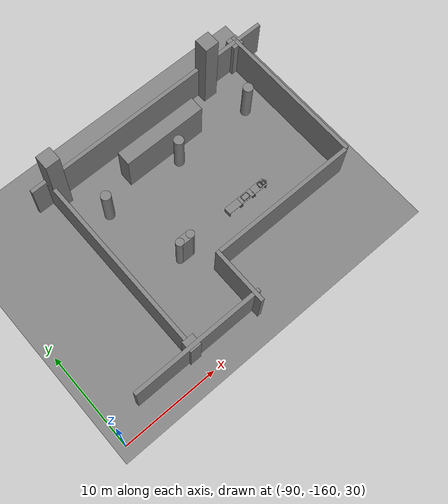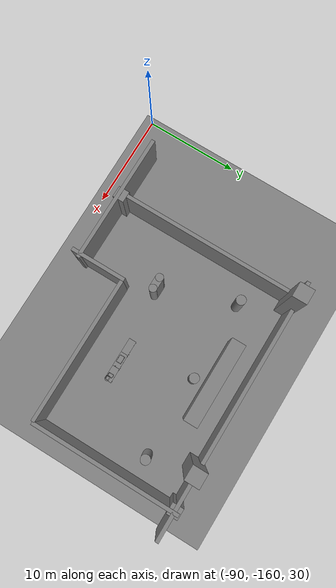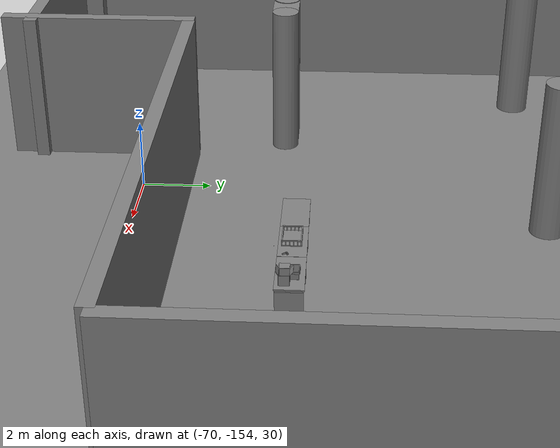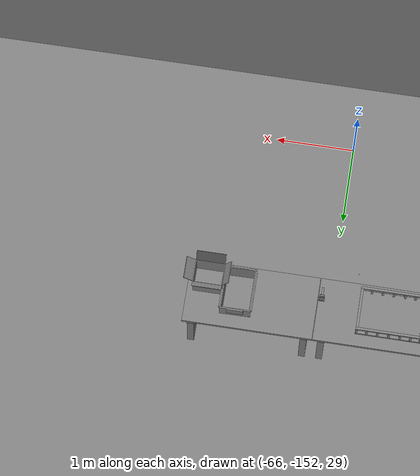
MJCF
<mujoco>
    <option gravity="0.000000000 0.000000000 -9.810000420" timestep="0.0049999999" integrator="implicitfast" density="1.225" viscosity="1.8000001e-05" noslip_iterations="10" iterations="100" sdf_iterations="50">
        <flag multiccd="disable"/>
    </option>
    <size memory="1000M"/>
    <compiler coordinate="local"/>
    <worldbody>
        <light cutoff="30" pos="0 1 1" dir="0 -1 -2"/>
        <light cutoff="30" pos="0 -1 1" dir="0 1 -2"/>
        <body pos="-64.866622925 -149.383972168 30.183746338" euler="89.999992371 89.999946594 0.000000000" name="openloong_gripper_2f85_fix_base_usda_bluebox_01">
            <geom contype="1" conaffinity="1" density="1000" type="box" material="" rgba="0.500000000 0.500000000 0.500000000 1.000000000" solimp="0.899999976 0.949999988 0.001000000" friction="1.000000000 0.005000000 0.000100000" solref="0.020000000 1.000000000" margin="0" condim="3" group="0" pos="0.276596069 0.187225342 0.000061035" quat="0.707107008 0.000077501 0.707106471 0.000077456" size="0.100000001 0.057999998 0.010000000" name="openloong_gripper_2f85_fix_base_usda_geom_DF1ECC97_8EF7_48F7_829C_9F771E168BCC"/>
            <geom contype="1" conaffinity="1" density="1000" type="box" material="" rgba="0.500000000 0.500000000 0.500000000 1.000000000" solimp="0.899999976 0.949999988 0.001000000" friction="1.000000000 0.005000000 0.000100000" solref="0.020000000 1.000000000" margin="0" condim="3" group="0" pos="0.000000000 0.002883911 0.000000000" quat="1.000000000 0.000000000 0.000000000 0.000000000" size="0.254000008 0.003000000 0.172000006" name="openloong_gripper_2f85_fix_base_usda_geom_2117D12B_2982_4BAC_B174_14F00A71CDA5"/>
            <geom contype="1" conaffinity="1" density="1000" type="box" material="" rgba="0.500000000 0.500000000 0.500000000 1.000000000" solimp="0.899999976 0.949999988 0.001000000" friction="1.000000000 0.005000000 0.000100000" solref="0.020000000 1.000000000" margin="0" condim="3" group="0" pos="0.000015259 0.124874115 0.173477173" quat="0.999796450 0.020176515 -0.000000015 0.000000030" size="0.259999990 0.119999997 0.007000000" name="openloong_gripper_2f85_fix_base_usda_geom_03704B3F_1BBF_469C_B600_882E7DF722FA"/>
            <geom contype="1" conaffinity="1" density="1000" type="box" material="" rgba="0.500000000 0.500000000 0.500000000 1.000000000" solimp="0.899999976 0.949999988 0.001000000" friction="1.000000000 0.005000000 0.000100000" solref="0.020000000 1.000000000" margin="0" condim="3" group="0" pos="0.000015259 0.124874115 -0.173477173" quat="0.999796450 -0.020176545 -0.000000015 0.000000000" size="0.259999990 0.119999997 0.007000000" name="openloong_gripper_2f85_fix_base_usda_geom_D5048339_3377_4BEC_ACAD_41E0266F5590"/>
            <geom contype="1" conaffinity="1" density="1000" type="box" material="" rgba="0.500000000 0.500000000 0.500000000 1.000000000" solimp="0.899999976 0.949999988 0.001000000" friction="1.000000000 0.005000000 0.000100000" solref="0.020000000 1.000000000" margin="0" condim="3" group="0" pos="0.000015259 0.214012146 0.188980103" quat="0.999913096 0.013176724 0.000000015 0.000000000" size="0.259999990 0.029999999 0.012500000" name="openloong_gripper_2f85_fix_base_usda_geom_668A6E18_7C99_42C5_AD70_ABF84F4898E9"/>
            <geom contype="1" conaffinity="1" density="1000" type="box" material="" rgba="0.500000000 0.500000000 0.500000000 1.000000000" solimp="0.899999976 0.949999988 0.001000000" friction="1.000000000 0.005000000 0.000100000" solref="0.020000000 1.000000000" margin="0" condim="3" group="0" pos="-0.258346558 0.125289917 0.001876831" quat="0.702796996 -0.020792052 0.710783184 0.020769238" size="0.189999998 0.119999997 0.009000000" name="openloong_gripper_2f85_fix_base_usda_geom_2AEA9CF5_EBBA_4ADE_B23B_AE190CB9D988"/>
            <geom contype="1" conaffinity="1" density="1000" type="box" material="" rgba="0.500000000 0.500000000 0.500000000 1.000000000" solimp="0.899999976 0.949999988 0.001000000" friction="1.000000000 0.005000000 0.000100000" solref="0.020000000 1.000000000" margin="0" condim="3" group="0" pos="0.000015259 0.214012146 -0.188980103" quat="0.999913096 -0.013176769 0.000000030 0.000000015" size="0.259999990 0.029999999 0.012500000" name="openloong_gripper_2f85_fix_base_usda_geom_886D1551_F9D8_422F_9EB8_9A3F76985359"/>
            <geom contype="1" conaffinity="1" density="1000" type="box" material="" rgba="0.500000000 0.500000000 0.500000000 1.000000000" solimp="0.899999976 0.949999988 0.001000000" friction="1.000000000 0.005000000 0.000100000" solref="0.020000000 1.000000000" margin="0" condim="3" group="0" pos="-0.276596069 0.187225342 0.000061035" quat="0.707106650 0.000077441 0.707106709 0.000077456" size="0.100000001 0.057999998 0.010000000" name="openloong_gripper_2f85_fix_base_usda_geom_DEFF2CF6_CAAA_499F_82EE_AB32FFD9D685"/>
            <geom contype="1" conaffinity="1" density="1000" type="box" material="" rgba="0.500000000 0.500000000 0.500000000 1.000000000" solimp="0.899999976 0.949999988 0.001000000" friction="1.000000000 0.005000000 0.000100000" solref="0.020000000 1.000000000" margin="0" condim="3" group="0" pos="0.258346558 0.125289917 0.001876831" quat="0.702851534 0.018856451 0.710823834 -0.019329429" size="0.189999998 0.119999997 0.009000000" name="openloong_gripper_2f85_fix_base_usda_geom_8468DE99_B9F8_40C6_8615_3C7EA072BF60"/>
            <freejoint name="openloong_gripper_2f85_fix_base_usda_bluebox_01_joint"/>
            <site size="0.005000000 0.005000000 0.005000000" rgba="0.500000000 0.500000000 0.500000000 1.000000000" pos="0.000000000 0.000000000 0.000000000" quat="0.999961913 0.008726534 0.000000000 0.000000000" group="0" type="sphere" name="openloong_gripper_2f85_fix_base_usda_bluebox_01site"/>
        </body>
        <body pos="-64.496299744 -149.491867065 30.235729218" euler="0.000000000 0.000000000 89.999946594" name="openloong_gripper_2f85_fix_base_usda_cardboardbox_01">
            <geom contype="1" conaffinity="1" density="1000" type="box" material="" rgba="0.500000000 0.500000000 0.500000000 1.000000000" solimp="0.899999976 0.949999988 0.001000000" friction="1.000000000 0.005000000 0.000100000" solref="0.020000000 1.000000000" margin="0" condim="3" group="0" pos="-0.003166199 -0.004086494 0.005052090" quat="1.000000000 0.000000000 0.000000000 0.000000000" size="0.142499998 0.177500010 0.005000000" name="openloong_gripper_2f85_fix_base_usda_geom_4CF64B56_11DE_46DD_9382_E781726B71A3"/>
            <geom contype="1" conaffinity="1" density="1000" type="box" material="" rgba="0.500000000 0.500000000 0.500000000 1.000000000" solimp="0.899999976 0.949999988 0.001000000" friction="1.000000000 0.005000000 0.000100000" solref="0.020000000 1.000000000" margin="0" condim="3" group="0" pos="-0.003166199 0.170316696 0.150570869" quat="1.000000000 0.000000000 0.000000000 0.000000000" size="0.142499998 0.005000000 0.149999991" name="openloong_gripper_2f85_fix_base_usda_geom_CF709D01_FE9B_4820_8D45_3511A667CEE6"/>
            <geom contype="1" conaffinity="1" density="1000" type="box" material="" rgba="0.500000000 0.500000000 0.500000000 1.000000000" solimp="0.899999976 0.949999988 0.001000000" friction="1.000000000 0.005000000 0.000100000" solref="0.020000000 1.000000000" margin="0" condim="3" group="0" pos="-0.147399902 -0.005307198 0.150570869" quat="1.000000000 0.000000000 0.000000000 0.000000000" size="0.005000000 0.177500010 0.149999991" name="openloong_gripper_2f85_fix_base_usda_geom_A3785E13_30F8_4509_87EC_D1C8E7F18986"/>
            <geom contype="1" conaffinity="1" density="1000" type="box" material="" rgba="0.500000000 0.500000000 0.500000000 1.000000000" solimp="0.899999976 0.949999988 0.001000000" friction="1.000000000 0.005000000 0.000100000" solref="0.020000000 1.000000000" margin="0" condim="3" group="0" pos="0.140275955 -0.005307198 0.150570869" quat="1.000000000 0.000000000 0.000000000 0.000000000" size="0.005000000 0.177500010 0.149999991" name="openloong_gripper_2f85_fix_base_usda_geom_E358B815_1C75_43FC_AE41_1F12B8325CE1"/>
            <geom contype="1" conaffinity="1" density="1000" type="box" material="" rgba="0.500000000 0.500000000 0.500000000 1.000000000" solimp="0.899999976 0.949999988 0.001000000" friction="1.000000000 0.005000000 0.000100000" solref="0.020000000 1.000000000" margin="0" condim="3" group="0" pos="-0.003166199 -0.181550980 0.150570869" quat="1.000000000 0.000000000 0.000000000 0.000000000" size="0.142499998 0.005000000 0.149999991" name="openloong_gripper_2f85_fix_base_usda_geom_A096108B_F68D_4ED6_9D08_2CDF07963D50"/>
            <freejoint name="openloong_gripper_2f85_fix_base_usda_cardboardbox_01_joint"/>
            <site size="0.005000000 0.005000000 0.005000000" rgba="0.500000000 0.500000000 0.500000000 1.000000000" pos="0.000000000 0.000000000 0.000000000" quat="0.999961913 0.008726535 0.000000000 0.000000000" group="0" type="sphere" name="openloong_gripper_2f85_fix_base_usda_site_96CB5760_9E9F_419F_9014_026DCC1A613B"/>
            <body pos="0.139160156 -0.004048347 0.301930904" euler="-179.999954224 49.383502960 179.999954224" name="openloong_gripper_2f85_fix_base_usda_A1_006">
                <geom contype="1" conaffinity="1" density="1000" type="box" material="" rgba="0.500000000 0.500000000 0.500000000 1.000000000" solimp="0.899999976 0.949999988 0.001000000" friction="1.000000000 0.005000000 0.000100000" solref="0.020000000 1.000000000" margin="0" condim="3" group="0" pos="-0.071587563 0.000009537 0.001745224" quat="0.999999881 0.000000000 0.000000000 0.000000000" size="0.071249999 0.179999992 0.002500000" name="openloong_gripper_2f85_fix_base_usda_geom_21BBDA60_BC5C_44BD_9A6F_49DEACCCC40C"/>
                <joint armature="0" stiffness="0.07" damping="0.0099999998" axis="0.000000 1.000000 0.000000" type="hinge" name="openloong_gripper_2f85_fix_base_usda_A1_006"/>
            </body>
            <body pos="-0.145902634 -0.004086494 0.301938057" euler="-180.000000000 -60.000011444 -180.000000000" name="openloong_gripper_2f85_fix_base_usda_A2_006">
                <geom contype="1" conaffinity="1" density="1000" type="box" material="" rgba="0.500000000 0.500000000 0.500000000 1.000000000" solimp="0.899999976 0.949999988 0.001000000" friction="1.000000000 0.005000000 0.000100000" solref="0.020000000 1.000000000" margin="0" condim="3" group="0" pos="0.071268082 0.000009537 0.002717972" quat="0.000002921 0.000000000 -0.000000030 0.999999881" size="0.071249999 0.179999992 0.002500000" name="openloong_gripper_2f85_fix_base_usda_geom_79F82A4D_1548_4586_83DA_A6CFD9221831"/>
                <joint armature="0" stiffness="0.07" damping="0.0099999998" axis="0.000000 1.000000 0.000000" type="hinge" name="openloong_gripper_2f85_fix_base_usda_A2_006"/>
            </body>
            <body pos="-0.003385544 0.175991058 0.301930904" euler="-125.858116150 -0.000004561 0.000002331" name="openloong_gripper_2f85_fix_base_usda_B2_006">
                <geom contype="1" conaffinity="1" density="1000" type="box" material="" rgba="0.500000000 0.500000000 0.500000000 1.000000000" solimp="0.899999976 0.949999988 0.001000000" friction="1.000000000 0.005000000 0.000100000" solref="0.020000000 1.000000000" margin="0" condim="3" group="0" pos="0.000009537 -0.070939064 -0.002470016" quat="0.999614120 0.027776197 -0.000000015 0.000000030" size="0.137500003 0.064999998 0.005000000" name="openloong_gripper_2f85_fix_base_usda_geom_28911DBC_E43D_43E1_BB08_D176C8FC71D6"/>
                <joint armature="0" stiffness="0.07" damping="0.0099999998" axis="1.000000 0.000000 0.000000" type="hinge" name="openloong_gripper_2f85_fix_base_usda_B2_006"/>
            </body>
            <body pos="-0.003385544 -0.184140205 0.301938057" euler="147.805557251 0.000000000 0.000000000" name="openloong_gripper_2f85_fix_base_usda_B1_006">
                <geom contype="1" conaffinity="1" density="1000" type="box" material="" rgba="0.500000000 0.500000000 0.500000000 1.000000000" solimp="0.899999976 0.949999988 0.001000000" friction="1.000000000 0.005000000 0.000100000" solref="0.020000000 1.000000000" margin="0" condim="3" group="0" pos="-0.000028610 0.070202351 -0.002703667" quat="0.999614179 -0.027776167 0.000000000 0.000000000" size="0.137500003 0.064999998 0.005000000" name="openloong_gripper_2f85_fix_base_usda_geom_8B1B117E_0286_4075_8A1F_43F657DFA917"/>
                <joint armature="0" stiffness="0.07" damping="0.0099999998" axis="1.000000 0.000000 0.000000" type="hinge" name="openloong_gripper_2f85_fix_base_usda_B1_006"/>
            </body>
        </body>
        <body pos="-65.882858276 -149.481979370 30.229999542" euler="-64.487716675 0.000000000 0.000000000" name="openloong_gripper_2f85_fix_base_usda_Barcode">
            <geom contype="1" conaffinity="1" density="1000" type="box" material="" rgba="0.500000000 0.500000000 0.500000000 1.000000000" solimp="0.899999976 0.949999988 0.001000000" friction="1.000000000 0.005000000 0.000100000" solref="0.020000000 1.000000000" margin="0" condim="3" group="0" pos="0.000000000 0.013038635 0.001419067" quat="0.000000000 0.000000000 0.000000000 1.000000119" size="0.034000002 0.010000000 0.017999999" name="openloong_gripper_2f85_fix_base_usda_geom_900A1CF8_CEC6_42CE_9E78_4D8E52665917"/>
            <geom contype="1" conaffinity="1" density="1000" type="box" material="" rgba="0.500000000 0.500000000 0.500000000 1.000000000" solimp="0.899999976 0.949999988 0.001000000" friction="1.000000000 0.005000000 0.000100000" solref="0.020000000 1.000000000" margin="0" condim="3" group="0" pos="0.000000000 -0.035301208 -0.007095337" quat="0.000000000 0.000000000 -0.043619365 0.999048233" size="0.028999999 0.010000000 0.020000000" name="openloong_gripper_2f85_fix_base_usda_geom_CBDCE38A_88D3_4C56_AF40_CBE08AA59A3B"/>
            <geom contype="1" conaffinity="1" density="1000" type="box" material="" rgba="0.500000000 0.500000000 0.500000000 1.000000000" solimp="0.899999976 0.949999988 0.001000000" friction="1.000000000 0.005000000 0.000100000" solref="0.020000000 1.000000000" margin="0" condim="3" group="0" pos="0.000000000 -0.043411255 -0.011749268" quat="0.922262907 0.386563420 0.000000000 0.000000000" size="0.026000001 0.010000000 0.020000000" name="openloong_gripper_2f85_fix_base_usda_geom_02EA8CF1_59DF_4AB1_9533_CC84FA20EB65"/>
            <geom contype="1" conaffinity="1" density="1000" type="box" material="" rgba="0.500000000 0.500000000 0.500000000 1.000000000" solimp="0.899999976 0.949999988 0.001000000" friction="1.000000000 0.005000000 0.000100000" solref="0.020000000 1.000000000" margin="0" condim="3" group="0" pos="0.000000000 -0.016967773 -0.031860352" quat="0.000000000 0.000000000 0.000000000 1.000000119" size="0.008000000 0.010000000 0.013000000" name="openloong_gripper_2f85_fix_base_usda_geom_932DEF92_663F_4FF1_B19F_C877974C247F"/>
            <geom contype="1" conaffinity="1" density="1000" type="box" material="" rgba="0.500000000 0.500000000 0.500000000 1.000000000" solimp="0.899999976 0.949999988 0.001000000" friction="1.000000000 0.005000000 0.000100000" solref="0.020000000 1.000000000" margin="0" condim="3" group="0" pos="0.000000000 -0.001869202 0.000312805" quat="0.953716993 0.300705761 0.000000000 0.000000000" size="0.032000002 0.010000000 0.018999999" name="openloong_gripper_2f85_fix_base_usda_geom_C5618FCF_24C5_483D_82E1_3F961911ED6C"/>
            <geom contype="1" conaffinity="1" density="1000" type="box" material="" rgba="0.500000000 0.500000000 0.500000000 1.000000000" solimp="0.899999976 0.949999988 0.001000000" friction="1.000000000 0.005000000 0.000100000" solref="0.020000000 1.000000000" margin="0" condim="3" group="0" pos="0.000000000 -0.019531250 -0.003173828" quat="0.953716993 0.300705761 0.000000000 0.000000000" size="0.030999999 0.010000000 0.020000000" name="openloong_gripper_2f85_fix_base_usda_geom_EC7E60C7_2F62_49BE_BB13_4B0042FE911C"/>
            <geom contype="1" conaffinity="1" density="1000" type="box" material="" rgba="0.500000000 0.500000000 0.500000000 1.000000000" solimp="0.899999976 0.949999988 0.001000000" friction="1.000000000 0.005000000 0.000100000" solref="0.020000000 1.000000000" margin="0" condim="3" group="0" pos="0.000000000 -0.035301208 -0.007095337" quat="0.953716993 0.300705761 0.000000000 0.000000000" size="0.028999999 0.010000000 0.020000000" name="openloong_gripper_2f85_fix_base_usda_geom_F4D9AFEB_EA65_43B9_B4B6_93E699B709F3"/>
            <geom contype="1" conaffinity="1" density="1000" type="box" material="" rgba="0.500000000 0.500000000 0.500000000 1.000000000" solimp="0.899999976 0.949999988 0.001000000" friction="1.000000000 0.005000000 0.000100000" solref="0.020000000 1.000000000" margin="0" condim="3" group="0" pos="0.000000000 -0.042617798 -0.071121216" quat="0.000000000 0.000000000 0.000000000 1.000000119" size="0.013000000 0.021000000 0.059999999" name="openloong_gripper_2f85_fix_base_usda_geom_2A3E8045_8A88_4175_848D_CFE757CAE3CB"/>
            <freejoint name="openloong_gripper_2f85_fix_base_usda_Barcode_joint"/>
            <site size="0.005000000 0.005000000 0.005000000" rgba="0.500000000 0.500000000 0.500000000 1.000000000" pos="0.000000000 0.000000000 0.000000000" quat="1.000000000 0.000000000 0.000000000 0.000000000" group="0" type="sphere" name="openloong_gripper_2f85_fix_base_usda_Barcode_site"/>
        </body>
        <body pos="-66.745018005 -149.392349243 30.184000015" euler="0.000000000 0.000000000 89.999946594" name="[22329749018681]_Basket_01">
            <geom contype="1" conaffinity="1" density="1000" type="box" material="" rgba="0.500000000 0.500000000 0.500000000 1.000000000" solimp="0.899999976 0.949999988 0.001000000" friction="1.000000000 0.005000000 0.000100000" solref="0.020000000 1.000000000" margin="0" condim="3" group="0" pos="-0.052425385 0.389207840 0.089787483" quat="0.707107008 0.000000000 0.000000000 0.707106411" size="0.014249999 0.014249999 0.059999999" name="[22329749018681]_geom_C27F29F6_61FB_473A_9DB8_AA5EF8A51C4C"/>
            <geom contype="1" conaffinity="1" density="1000" type="box" material="" rgba="0.500000000 0.500000000 0.500000000 1.000000000" solimp="0.899999976 0.949999988 0.001000000" friction="1.000000000 0.005000000 0.000100000" solref="0.020000000 1.000000000" margin="0" condim="3" group="0" pos="0.264015198 -0.133043289 0.089787483" quat="0.707107008 0.000000000 0.000000000 0.707106411" size="0.014249999 0.014249999 0.059999999" name="[22329749018681]_geom_63677043_F429_4F1A_89D2_44A0025BFF58"/>
            <geom contype="1" conaffinity="1" density="1000" type="box" material="" rgba="0.500000000 0.500000000 0.500000000 1.000000000" solimp="0.899999976 0.949999988 0.001000000" friction="1.000000000 0.005000000 0.000100000" solref="0.020000000 1.000000000" margin="0" condim="3" group="0" pos="-0.264015198 -0.265548706 0.089793205" quat="0.707107008 0.000000000 0.000000000 0.707106411" size="0.014249999 0.014249999 0.059999999" name="[22329749018681]_geom_94BD12DC_920B_45C4_AD33_F0435D640983"/>
            <geom contype="1" conaffinity="1" density="1000" type="box" material="" rgba="0.500000000 0.500000000 0.500000000 1.000000000" solimp="0.899999976 0.949999988 0.001000000" friction="1.000000000 0.005000000 0.000100000" solref="0.020000000 1.000000000" margin="0" condim="3" group="0" pos="-0.160263062 -0.389322281 0.089793205" quat="0.707107008 0.000000000 0.000000000 0.707106411" size="0.014249999 0.014249999 0.059999999" name="[22329749018681]_geom_BFB1CE2E_9E99_4F63_BCFE_DA8434ED5D19"/>
            <geom contype="1" conaffinity="1" density="1000" type="box" material="" rgba="0.500000000 0.500000000 0.500000000 1.000000000" solimp="0.899999976 0.949999988 0.001000000" friction="1.000000000 0.005000000 0.000100000" solref="0.020000000 1.000000000" margin="0" condim="3" group="0" pos="0.162265778 -0.389322281 0.089787483" quat="0.707107008 0.000000000 0.000000000 0.707106411" size="0.014249999 0.014249999 0.059999999" name="[22329749018681]_geom_34EA9BDF_43D9_4F36_9EE7_4EB0929666DC"/>
            <geom contype="1" conaffinity="1" density="1000" type="box" material="" rgba="0.500000000 0.500000000 0.500000000 1.000000000" solimp="0.899999976 0.949999988 0.001000000" friction="1.000000000 0.005000000 0.000100000" solref="0.020000000 1.000000000" margin="0" condim="3" group="0" pos="0.264015198 0.389207840 0.089787483" quat="0.707107008 0.000000000 0.000000000 0.707106411" size="0.014249999 0.014249999 0.059999999" name="[22329749018681]_geom_1C2E0BFA_3814_4839_9270_E7DEEE729740"/>
            <geom contype="1" conaffinity="1" density="1000" type="box" material="" rgba="0.500000000 0.500000000 0.500000000 1.000000000" solimp="0.899999976 0.949999988 0.001000000" friction="1.000000000 0.005000000 0.000100000" solref="0.020000000 1.000000000" margin="0" condim="3" group="0" pos="-0.264015198 -0.133043289 0.089793205" quat="0.707107008 0.000000000 0.000000000 0.707106411" size="0.014249999 0.014249999 0.059999999" name="[22329749018681]_geom_B16CD10E_5D6C_4CA1_80A8_6BEC4B17F458"/>
            <geom contype="1" conaffinity="1" density="1000" type="box" material="" rgba="0.500000000 0.500000000 0.500000000 1.000000000" solimp="0.899999976 0.949999988 0.001000000" friction="1.000000000 0.005000000 0.000100000" solref="0.020000000 1.000000000" margin="0" condim="3" group="0" pos="-0.264026642 0.269256592 0.089793205" quat="0.707107008 0.000000000 0.000000000 0.707106411" size="0.014249999 0.014249999 0.059999999" name="[22329749018681]_geom_B1CD000B_A899_4FD1_BECD_3CEBC243324D"/>
            <geom contype="1" conaffinity="1" density="1000" type="box" material="" rgba="0.500000000 0.500000000 0.500000000 1.000000000" solimp="0.899999976 0.949999988 0.001000000" friction="1.000000000 0.005000000 0.000100000" solref="0.020000000 1.000000000" margin="0" condim="3" group="0" pos="0.054462433 0.389207840 0.089787483" quat="0.707107008 0.000000000 0.000000000 0.707106411" size="0.014249999 0.014249999 0.059999999" name="[22329749018681]_geom_39582475_AA34_44DA_B91D_35284B619FA1"/>
            <geom contype="1" conaffinity="1" density="1000" type="box" material="" rgba="0.500000000 0.500000000 0.500000000 1.000000000" solimp="0.899999976 0.949999988 0.001000000" friction="1.000000000 0.005000000 0.000100000" solref="0.020000000 1.000000000" margin="0" condim="3" group="0" pos="0.054462433 -0.389322281 0.089787483" quat="0.707107008 0.000000000 0.000000000 0.707106411" size="0.014249999 0.014249999 0.059999999" name="[22329749018681]_geom_1E939D2E_FB51_4BC9_9EF8_BD61BD7222AD"/>
            <geom contype="1" conaffinity="1" density="1000" type="box" material="" rgba="0.500000000 0.500000000 0.500000000 1.000000000" solimp="0.899999976 0.949999988 0.001000000" friction="1.000000000 0.005000000 0.000100000" solref="0.020000000 1.000000000" margin="0" condim="3" group="0" pos="0.264015198 0.269256592 0.089793205" quat="0.707107008 0.000000000 0.000000000 0.707106411" size="0.014249999 0.014249999 0.059999999" name="[22329749018681]_geom_4D50C39B_1F00_4214_B483_1E2E9C212BDF"/>
            <geom contype="1" conaffinity="1" density="1000" type="box" material="" rgba="0.500000000 0.500000000 0.500000000 1.000000000" solimp="0.899999976 0.949999988 0.001000000" friction="1.000000000 0.005000000 0.000100000" solref="0.020000000 1.000000000" margin="0" condim="3" group="0" pos="0.264015198 -0.389322281 0.089787483" quat="0.707107008 0.000000000 0.000000000 0.707106411" size="0.014249999 0.014249999 0.059999999" name="[22329749018681]_geom_120D0737_5E55_4EAA_9B42_18EB81440B9A"/>
            <geom contype="1" conaffinity="1" density="1000" type="box" material="" rgba="0.500000000 0.500000000 0.500000000 1.000000000" solimp="0.899999976 0.949999988 0.001000000" friction="1.000000000 0.005000000 0.000100000" solref="0.020000000 1.000000000" margin="0" condim="3" group="0" pos="0.000000000 0.000000000 0.015998840" quat="0.707107008 0.000000000 0.000000000 0.707106411" size="0.403499991 0.279000014 0.015750000" name="[22329749018681]_geom_29FBE751_5D67_443D_9753_F6C6A27E84B0"/>
            <geom contype="1" conaffinity="1" density="1000" type="box" material="" rgba="0.500000000 0.500000000 0.500000000 1.000000000" solimp="0.899999976 0.949999988 0.001000000" friction="1.000000000 0.005000000 0.000100000" solref="0.020000000 1.000000000" margin="0" condim="3" group="0" pos="0.000000000 -0.389476776 0.163619041" quat="0.707107008 0.000000000 0.000000000 0.707106411" size="0.015000000 0.277500004 0.015750000" name="[22329749018681]_geom_A1CFAD43_8DCE_41D7_ADE8_5A8E194058CE"/>
            <geom contype="1" conaffinity="1" density="1000" type="box" material="" rgba="0.500000000 0.500000000 0.500000000 1.000000000" solimp="0.899999976 0.949999988 0.001000000" friction="1.000000000 0.005000000 0.000100000" solref="0.020000000 1.000000000" margin="0" condim="3" group="0" pos="0.162265778 0.389207840 0.089787483" quat="0.707107008 0.000000000 0.000000000 0.707106411" size="0.014249999 0.014249999 0.059999999" name="[22329749018681]_geom_B57BD950_B1F9_42F5_9EF9_52F02818B014"/>
            <geom contype="1" conaffinity="1" density="1000" type="box" material="" rgba="0.500000000 0.500000000 0.500000000 1.000000000" solimp="0.899999976 0.949999988 0.001000000" friction="1.000000000 0.005000000 0.000100000" solref="0.020000000 1.000000000" margin="0" condim="3" group="0" pos="0.000000000 0.389471054 0.163619041" quat="0.707107008 0.000000000 0.000000000 0.707106411" size="0.015000000 0.277500004 0.015750000" name="[22329749018681]_geom_FF4DA2D4_38DA_4151_A473_C1D7E0AC2C28"/>
            <geom contype="1" conaffinity="1" density="1000" type="box" material="" rgba="0.500000000 0.500000000 0.500000000 1.000000000" solimp="0.899999976 0.949999988 0.001000000" friction="1.000000000 0.005000000 0.000100000" solref="0.020000000 1.000000000" margin="0" condim="3" group="0" pos="-0.263511658 0.000000000 0.163619041" quat="0.707107008 0.000000000 0.000000000 0.707106411" size="0.403499991 0.015000000 0.015750000" name="[22329749018681]_geom_85E50096_DD52_4687_AA9E_0CDC7B9C7746"/>
            <geom contype="1" conaffinity="1" density="1000" type="box" material="" rgba="0.500000000 0.500000000 0.500000000 1.000000000" solimp="0.899999976 0.949999988 0.001000000" friction="1.000000000 0.005000000 0.000100000" solref="0.020000000 1.000000000" margin="0" condim="3" group="0" pos="-0.264015198 0.141334534 0.089793205" quat="0.707107008 0.000000000 0.000000000 0.707106411" size="0.014249999 0.014249999 0.059999999" name="[22329749018681]_geom_79E86E22_20D4_4F90_97E0_0119E2C4417F"/>
            <geom contype="1" conaffinity="1" density="1000" type="box" material="" rgba="0.500000000 0.500000000 0.500000000 1.000000000" solimp="0.899999976 0.949999988 0.001000000" friction="1.000000000 0.005000000 0.000100000" solref="0.020000000 1.000000000" margin="0" condim="3" group="0" pos="0.264015198 -0.265548706 0.089787483" quat="0.707107008 0.000000000 0.000000000 0.707106411" size="0.014249999 0.014249999 0.059999999" name="[22329749018681]_geom_AD52EE42_EA0A_4199_BBC1_7190B4137140"/>
            <geom contype="1" conaffinity="1" density="1000" type="box" material="" rgba="0.500000000 0.500000000 0.500000000 1.000000000" solimp="0.899999976 0.949999988 0.001000000" friction="1.000000000 0.005000000 0.000100000" solref="0.020000000 1.000000000" margin="0" condim="3" group="0" pos="-0.160263062 0.389207840 0.089787483" quat="0.707107008 0.000000000 0.000000000 0.707106411" size="0.014249999 0.014249999 0.059999999" name="[22329749018681]_geom_3B1A6F2F_4BCE_47BA_B98B_C01044E371D8"/>
            <geom contype="1" conaffinity="1" density="1000" type="box" material="" rgba="0.500000000 0.500000000 0.500000000 1.000000000" solimp="0.899999976 0.949999988 0.001000000" friction="1.000000000 0.005000000 0.000100000" solref="0.020000000 1.000000000" margin="0" condim="3" group="0" pos="-0.052425385 -0.389322281 0.089787483" quat="0.707107008 0.000000000 0.000000000 0.707106411" size="0.014249999 0.014249999 0.059999999" name="[22329749018681]_geom_8C1FE14A_5997_4F88_AED5_7B5DE3FB0451"/>
            <geom contype="1" conaffinity="1" density="1000" type="box" material="" rgba="0.500000000 0.500000000 0.500000000 1.000000000" solimp="0.899999976 0.949999988 0.001000000" friction="1.000000000 0.005000000 0.000100000" solref="0.020000000 1.000000000" margin="0" condim="3" group="0" pos="-0.264026642 -0.389322281 0.089793205" quat="0.707107008 0.000000000 0.000000000 0.707106411" size="0.014249999 0.014249999 0.059999999" name="[22329749018681]_geom_E55EDCBA_2ED9_42C0_A6BE_27295611E78D"/>
            <geom contype="1" conaffinity="1" density="1000" type="box" material="" rgba="0.500000000 0.500000000 0.500000000 1.000000000" solimp="0.899999976 0.949999988 0.001000000" friction="1.000000000 0.005000000 0.000100000" solref="0.020000000 1.000000000" margin="0" condim="3" group="0" pos="0.264015198 0.141334534 0.089787483" quat="0.707107008 0.000000000 0.000000000 0.707106411" size="0.014249999 0.014249999 0.059999999" name="[22329749018681]_geom_38854886_F3CE_4FD9_870F_49167D3F21A9"/>
            <geom contype="1" conaffinity="1" density="1000" type="box" material="" rgba="0.500000000 0.500000000 0.500000000 1.000000000" solimp="0.899999976 0.949999988 0.001000000" friction="1.000000000 0.005000000 0.000100000" solref="0.020000000 1.000000000" margin="0" condim="3" group="0" pos="-0.264015198 0.389207840 0.089793205" quat="0.707107008 0.000000000 0.000000000 0.707106411" size="0.014249999 0.014249999 0.059999999" name="[22329749018681]_geom_90BBE1B0_B13B_4C1F_A4E6_FB1CC24E38D4"/>
            <geom contype="1" conaffinity="1" density="1000" type="box" material="" rgba="0.500000000 0.500000000 0.500000000 1.000000000" solimp="0.899999976 0.949999988 0.001000000" friction="1.000000000 0.005000000 0.000100000" solref="0.020000000 1.000000000" margin="0" condim="3" group="0" pos="0.264015198 0.004480362 0.089787483" quat="0.707107008 0.000000000 0.000000000 0.707106411" size="0.014249999 0.014249999 0.059999999" name="[22329749018681]_geom_B12962AA_2132_4C1A_AFE4_BAF9086A1E8B"/>
            <geom contype="1" conaffinity="1" density="1000" type="box" material="" rgba="0.500000000 0.500000000 0.500000000 1.000000000" solimp="0.899999976 0.949999988 0.001000000" friction="1.000000000 0.005000000 0.000100000" solref="0.020000000 1.000000000" margin="0" condim="3" group="0" pos="0.263694763 -0.000011444 0.163619041" quat="0.707107008 0.000000000 0.000000000 0.707106411" size="0.403499991 0.015000000 0.015750000" name="[22329749018681]_geom_8975F7DA_7209_47C2_96EA_3ACF3E7FA570"/>
            <geom contype="1" conaffinity="1" density="1000" type="box" material="" rgba="0.500000000 0.500000000 0.500000000 1.000000000" solimp="0.899999976 0.949999988 0.001000000" friction="1.000000000 0.005000000 0.000100000" solref="0.020000000 1.000000000" margin="0" condim="3" group="0" pos="-0.264015198 0.004480362 0.089793205" quat="0.707107008 0.000000000 0.000000000 0.707106411" size="0.014249999 0.014249999 0.059999999" name="[22329749018681]_geom_69F8A425_FD56_44CE_B312_5B4BC310E6B8"/>
            <freejoint name="[22329749018681]_joint_B304EC60_2613_466B_AF4B_C439229EDCF4"/>
        </body>
        <body pos="0.000000000 0.000000000 0.000000000" euler="0.000000000 0.000000000 0.000000000" name="Static Objects_Static Objects">
            <geom contype="1" conaffinity="1" density="1000" type="box" material="" rgba="0.500000000 0.500000000 0.500000000 1.000000000" solimp="0.899999976 0.949999988 0.001000000" friction="1.000000000 0.005000000 0.000100000" solref="0.020000000 1.000000000" margin="0" condim="3" group="0" pos="-67.544113159 -149.365814209 29.727830887" quat="0.500000417 0.499999970 0.499999553 0.499999970" size="0.381000012 0.319999993 0.041000001" name="Static Objects_geom_F81F5DB5_C7C6_4648_B5D8_F9EE6EFFB80C"/>
            <geom contype="1" conaffinity="1" density="1000" type="box" material="" rgba="0.500000000 0.500000000 0.500000000 1.000000000" solimp="0.899999976 0.949999988 0.001000000" friction="1.000000000 0.005000000 0.000100000" solref="0.020000000 1.000000000" margin="0" condim="3" group="0" pos="-68.239501953 -149.365814209 30.086868286" quat="0.500000417 0.499999970 0.499999553 0.499999970" size="0.370999992 0.039500002 0.745000005" name="Static Objects_geom_B97C7638_E965_48F9_94FA_9B6B2804B097"/>
            <geom contype="1" conaffinity="1" density="1000" type="box" material="" rgba="0.500000000 0.500000000 0.500000000 1.000000000" solimp="0.899999976 0.949999988 0.001000000" friction="1.000000000 0.005000000 0.000100000" solref="0.020000000 1.000000000" margin="0" condim="3" group="0" pos="-68.239501953 -149.365814209 30.147235870" quat="0.500000417 0.499999970 0.499999553 0.499999970" size="0.400000006 0.022000000 0.800000012" name="Static Objects_geom_717B1DEE_BC41_445C_9DB7_B6D1D10FC480"/>
            <geom contype="1" conaffinity="1" density="1000" type="box" material="" rgba="0.500000000 0.500000000 0.500000000 1.000000000" solimp="0.899999976 0.949999988 0.001000000" friction="1.000000000 0.005000000 0.000100000" solref="0.020000000 1.000000000" margin="0" condim="3" group="0" pos="-68.934890747 -149.365814209 29.727830887" quat="0.500000417 0.499999970 0.499999553 0.499999970" size="0.381000012 0.319999993 0.041000001" name="Static Objects_geom_838BF9E9_A40F_4817_9DEE_3904D1884A75"/>
            <geom contype="1" conaffinity="1" density="1000" type="box" material="" rgba="0.500000000 0.500000000 0.500000000 1.000000000" solimp="0.899999976 0.949999988 0.001000000" friction="1.000000000 0.005000000 0.000100000" solref="0.020000000 1.000000000" margin="0" condim="3" group="0" pos="-68.239501953 -149.365814209 29.561563492" quat="0.500000417 0.499999970 0.499999553 0.499999970" size="0.020000000 0.022000000 0.660000026" name="Static Objects_geom_BBDEBE8F_4A9F_494C_A4FF_D090E54C486A"/>
            <geom contype="1" conaffinity="1" density="1000" type="box" material="" rgba="0.500000000 0.500000000 0.500000000 1.000000000" solimp="0.899999976 0.949999988 0.001000000" friction="1.000000000 0.005000000 0.000100000" solref="0.020000000 1.000000000" margin="0" condim="3" group="0" pos="-65.945671082 -149.365814209 29.727830887" quat="0.500000417 0.499999970 0.499999553 0.499999970" size="0.381000012 0.319999993 0.041000001" name="Static Objects_geom_B8BF801E_E9A9_4026_81DC_03A0DA050F5F"/>
            <geom contype="1" conaffinity="1" density="1000" type="box" material="" rgba="0.500000000 0.500000000 0.500000000 1.000000000" solimp="0.899999976 0.949999988 0.001000000" friction="1.000000000 0.005000000 0.000100000" solref="0.020000000 1.000000000" margin="0" condim="3" group="0" pos="-66.641059875 -149.365814209 30.086868286" quat="0.500000417 0.499999970 0.499999553 0.499999970" size="0.370999992 0.039500002 0.745000005" name="Static Objects_geom_F4A8FFEE_D653_423C_B15E_E02139D7E7FB"/>
            <geom contype="1" conaffinity="1" density="1000" type="box" material="" rgba="0.500000000 0.500000000 0.500000000 1.000000000" solimp="0.899999976 0.949999988 0.001000000" friction="1.000000000 0.005000000 0.000100000" solref="0.020000000 1.000000000" margin="0" condim="3" group="0" pos="-66.641059875 -149.365814209 30.147235870" quat="0.500000417 0.499999970 0.499999553 0.499999970" size="0.400000006 0.022000000 0.800000012" name="Static Objects_geom_4117CB00_AF76_48EB_8C39_D93F6BEDA2ED"/>
            <geom contype="1" conaffinity="1" density="1000" type="box" material="" rgba="0.500000000 0.500000000 0.500000000 1.000000000" solimp="0.899999976 0.949999988 0.001000000" friction="1.000000000 0.005000000 0.000100000" solref="0.020000000 1.000000000" margin="0" condim="3" group="0" pos="-67.336448669 -149.365814209 29.727830887" quat="0.500000417 0.499999970 0.499999553 0.499999970" size="0.381000012 0.319999993 0.041000001" name="Static Objects_geom_4D6F2E72_7AFE_40AB_81B1_EE78B40A4F33"/>
            <geom contype="1" conaffinity="1" density="1000" type="box" material="" rgba="0.500000000 0.500000000 0.500000000 1.000000000" solimp="0.899999976 0.949999988 0.001000000" friction="1.000000000 0.005000000 0.000100000" solref="0.020000000 1.000000000" margin="0" condim="3" group="0" pos="-66.641059875 -149.365814209 29.561563492" quat="0.500000417 0.499999970 0.499999553 0.499999970" size="0.020000000 0.022000000 0.660000026" name="Static Objects_geom_81A3A4BF_CC2D_46E0_8C21_065F4006A41C"/>
            <geom contype="1" conaffinity="1" density="1000" type="box" material="" rgba="0.500000000 0.500000000 0.500000000 1.000000000" solimp="0.899999976 0.949999988 0.001000000" friction="1.000000000 0.005000000 0.000100000" solref="0.020000000 1.000000000" margin="0" condim="3" group="0" pos="-64.338577271 -149.365814209 29.727830887" quat="0.500000417 0.499999970 0.499999553 0.499999970" size="0.381000012 0.319999993 0.041000001" name="Static Objects_geom_EAA603BB_3F42_413C_BFFF_426C27F09851"/>
            <geom contype="1" conaffinity="1" density="1000" type="box" material="" rgba="0.500000000 0.500000000 0.500000000 1.000000000" solimp="0.899999976 0.949999988 0.001000000" friction="1.000000000 0.005000000 0.000100000" solref="0.020000000 1.000000000" margin="0" condim="3" group="0" pos="-65.033966064 -149.365814209 30.086868286" quat="0.500000417 0.499999970 0.499999553 0.499999970" size="0.370999992 0.039500002 0.745000005" name="Static Objects_geom_BBDBC4A7_54AB_47A7_8D2F_1C774995F955"/>
            <geom contype="1" conaffinity="1" density="1000" type="box" material="" rgba="0.500000000 0.500000000 0.500000000 1.000000000" solimp="0.899999976 0.949999988 0.001000000" friction="1.000000000 0.005000000 0.000100000" solref="0.020000000 1.000000000" margin="0" condim="3" group="0" pos="-65.033966064 -149.365814209 30.147235870" quat="0.500000417 0.499999970 0.499999553 0.499999970" size="0.400000006 0.022000000 0.800000012" name="Static Objects_geom_DFDC44F0_C28D_40FD_AF65_BBAA7DD246E3"/>
            <geom contype="1" conaffinity="1" density="1000" type="box" material="" rgba="0.500000000 0.500000000 0.500000000 1.000000000" solimp="0.899999976 0.949999988 0.001000000" friction="1.000000000 0.005000000 0.000100000" solref="0.020000000 1.000000000" margin="0" condim="3" group="0" pos="-65.729354858 -149.365814209 29.727830887" quat="0.500000417 0.499999970 0.499999553 0.499999970" size="0.381000012 0.319999993 0.041000001" name="Static Objects_geom_542CAA9D_7FF8_4D9C_AA52_B0D3EC6E040B"/>
            <geom contype="1" conaffinity="1" density="1000" type="box" material="" rgba="0.500000000 0.500000000 0.500000000 1.000000000" solimp="0.899999976 0.949999988 0.001000000" friction="1.000000000 0.005000000 0.000100000" solref="0.020000000 1.000000000" margin="0" condim="3" group="0" pos="-65.033966064 -149.365814209 29.561563492" quat="0.500000417 0.499999970 0.499999553 0.499999970" size="0.020000000 0.022000000 0.660000026" name="Static Objects_geom_BA96E8FD_DD66_4CD2_A290_0AC8C13DA887"/>
            <geom contype="1" conaffinity="1" density="1000" type="box" material="" rgba="0.500000000 0.500000000 0.500000000 1.000000000" solimp="0.899999976 0.949999988 0.001000000" friction="1.000000000 0.005000000 0.000100000" solref="0.020000000 1.000000000" margin="0" condim="3" group="0" pos="-61.754566193 -137.853729248 33.906845093" quat="0.707107067 0.000000000 0.000000000 0.707106471" size="0.759999990 0.759999990 4.500000000" name="Static Objects_geom_98150F11_35E6_424A_9292_72ABEFD20D07"/>
            <geom contype="1" conaffinity="1" density="1000" type="box" material="" rgba="0.500000000 0.500000000 0.500000000 1.000000000" solimp="0.899999976 0.949999988 0.001000000" friction="1.000000000 0.005000000 0.000100000" solref="0.020000000 1.000000000" margin="0" condim="3" group="0" pos="-57.511135101 -144.927108765 31.707921982" quat="1.000000000 0.000000000 0.000000000 0.000000000" size="0.200000003 8.000000000 2.299999952" name="Static Objects_geom_3766F19E_B238_48D9_A92D_53FFF505CA32"/>
            <geom contype="1" conaffinity="1" density="1000" type="box" material="" rgba="0.500000000 0.500000000 0.500000000 1.000000000" solimp="0.899999976 0.949999988 0.001000000" friction="1.000000000 0.005000000 0.000100000" solref="0.020000000 1.000000000" margin="0" condim="3" group="0" pos="-80.517646790 -157.574050903 31.688196182" quat="0.707107067 0.000000000 0.000000000 0.707106471" size="0.600000024 0.600000024 2.299999952" name="Static Objects_geom_1209FAA5_8ACD_414E_B3BE_A65CF5BA1197"/>
            <geom contype="1" conaffinity="1" density="1000" type="box" material="" rgba="0.500000000 0.500000000 0.500000000 1.000000000" solimp="0.899999976 0.949999988 0.001000000" friction="1.000000000 0.005000000 0.000100000" solref="0.020000000 1.000000000" margin="0" condim="3" group="0" pos="-80.711044312 -147.414932251 31.666158676" quat="1.000000000 0.000000000 0.000000000 0.000000000" size="0.200000003 10.000000000 2.299999952" name="Static Objects_geom_FA5216B6_8FA6_4B3D_82E0_268E38DFF909"/>
            <geom contype="1" conaffinity="1" density="1000" type="box" material="" rgba="0.500000000 0.500000000 0.500000000 1.000000000" solimp="0.899999976 0.949999988 0.001000000" friction="1.000000000 0.005000000 0.000100000" solref="0.020000000 1.000000000" margin="0" condim="3" group="0" pos="-57.687217712 -137.434692383 31.688196182" quat="0.707107067 0.000000000 0.000000000 0.707106471" size="0.600000024 0.600000024 2.299999952" name="Static Objects_geom_47833207_9E7A_42A3_9D2F_73CC1EE8FA20"/>
            <geom contype="1" conaffinity="1" density="1000" type="box" material="" rgba="0.500000000 0.500000000 0.500000000 1.000000000" solimp="0.899999976 0.949999988 0.001000000" friction="1.000000000 0.005000000 0.000100000" solref="0.020000000 1.000000000" margin="0" condim="3" group="0" pos="-69.537033081 -140.263229370 31.714921951" quat="0.707107067 0.000000000 0.000000000 0.707106471" size="0.759999990 4.500000000 2.299999952" name="Static Objects_geom_151F35C9_9987_4B27_954D_B60573EC9858"/>
            <geom contype="1" conaffinity="1" density="1000" type="box" material="" rgba="0.500000000 0.500000000 0.500000000 1.000000000" solimp="0.899999976 0.949999988 0.001000000" friction="1.000000000 0.005000000 0.000100000" solref="0.020000000 1.000000000" margin="0" condim="3" group="0" pos="-80.073638916 -137.853713989 33.906845093" quat="0.707107067 0.000000000 0.000000000 0.707106471" size="0.759999990 0.759999990 4.500000000" name="Static Objects_geom_AA120746_0F4D_4FE2_A8DC_6823FD507634"/>
            <geom contype="1" conaffinity="1" density="1000" type="box" material="" rgba="0.500000000 0.500000000 0.500000000 1.000000000" solimp="0.899999976 0.949999988 0.001000000" friction="1.000000000 0.005000000 0.000100000" solref="0.020000000 1.000000000" margin="0" condim="3" group="0" pos="-73.406707764 -155.734664917 31.707921982" quat="1.000000000 0.000000000 0.000000000 0.000000000" size="0.200000003 3.000000000 2.299999952" name="Static Objects_geom_59525AE6_48DD_4B90_857B_802131991CE5"/>
            <geom contype="1" conaffinity="1" density="1000" type="box" material="" rgba="0.500000000 0.500000000 0.500000000 1.000000000" solimp="0.899999976 0.949999988 0.001000000" friction="1.000000000 0.005000000 0.000100000" solref="0.020000000 1.000000000" margin="0" condim="3" group="0" pos="-68.497543335 -137.448257446 31.707921982" quat="0.707107067 0.000000000 0.000000000 0.707106471" size="0.200000003 14.000000000 2.299999952" name="Static Objects_geom_2FB85DC8_7810_418B_BBE4_FECABDDAE19A"/>
            <geom contype="1" conaffinity="1" density="1000" type="cylinder" material="" rgba="0.500000000 0.500000000 0.500000000 1.000000000" solimp="0.899999976 0.949999988 0.001000000" friction="1.000000000 0.005000000 0.000100000" solref="0.020000000 1.000000000" margin="0" condim="3" group="0" pos="-68.868522644 -142.134506226 31.711090088" quat="0.707107067 0.000000000 0.000000000 0.707106471" size="0.509999990 2.299999952 1.000000000" name="Static Objects_geom_CDD63E48_8449_4283_B92A_66D9BEABE39F"/>
            <geom contype="1" conaffinity="1" density="1000" type="plane" material="" rgba="0.500000000 0.500000000 0.500000000 1.000000000" solimp="0.899999976 0.949999988 0.001000000" friction="1.000000000 0.005000000 0.000100000" solref="0.020000000 1.000000000" margin="0" condim="3" group="0" pos="-72.873703003 -147.131927490 29.409669876" quat="1.000000000 0.000000000 0.000000000 0.000000000" size="18.000000000 14.000000000 1.000000000" name="Static Objects_geom_8523296A_898B_494C_A91C_49872C968101"/>
            <geom contype="1" conaffinity="1" density="1000" type="box" material="" rgba="0.500000000 0.500000000 0.500000000 1.000000000" solimp="0.899999976 0.949999988 0.001000000" friction="1.000000000 0.005000000 0.000100000" solref="0.020000000 1.000000000" margin="0" condim="3" group="0" pos="-79.943580627 -157.782272339 31.707921982" quat="0.707107067 0.000000000 0.000000000 0.707106471" size="0.200000003 7.000000000 2.299999952" name="Static Objects_geom_43635279_6484_4C73_B9AD_D24A12798B23"/>
            <geom contype="1" conaffinity="1" density="1000" type="box" material="" rgba="0.500000000 0.500000000 0.500000000 1.000000000" solimp="0.899999976 0.949999988 0.001000000" friction="1.000000000 0.005000000 0.000100000" solref="0.020000000 1.000000000" margin="0" condim="3" group="0" pos="-65.421028137 -152.903442383 31.707921982" quat="0.707107067 0.000000000 0.000000000 0.707106471" size="0.200000003 7.800000191 2.299999952" name="Static Objects_geom_76675161_84C0_463E_82D1_98047DD44304"/>
            <geom contype="1" conaffinity="1" density="1000" type="box" material="" rgba="0.500000000 0.500000000 0.500000000 1.000000000" solimp="0.899999976 0.949999988 0.001000000" friction="1.000000000 0.005000000 0.000100000" solref="0.020000000 1.000000000" margin="0" condim="3" group="0" pos="-74.776908875 -149.964416504 31.688196182" quat="1.000000000 0.000000000 0.000000000 0.000000000" size="0.600000024 0.409999996 2.299999952" name="Static Objects_geom_891F9529_2B99_4EAA_BB4C_ED8721639FBB"/>
            <geom contype="1" conaffinity="1" density="1000" type="cylinder" material="" rgba="0.500000000 0.500000000 0.500000000 1.000000000" solimp="0.899999976 0.949999988 0.001000000" friction="1.000000000 0.005000000 0.000100000" solref="0.020000000 1.000000000" margin="0" condim="3" group="0" pos="-60.161884308 -142.134506226 31.711090088" quat="0.707107067 0.000000000 0.000000000 0.707106471" size="0.509999990 2.299999952 1.000000000" name="Static Objects_geom_B702ACC1_482A_4D4F_A9E4_1BF0F18A02E4"/>
            <geom contype="1" conaffinity="1" density="1000" type="cylinder" material="" rgba="0.500000000 0.500000000 0.500000000 1.000000000" solimp="0.899999976 0.949999988 0.001000000" friction="1.000000000 0.005000000 0.000100000" solref="0.020000000 1.000000000" margin="0" condim="3" group="0" pos="-75.382453918 -149.963455200 31.711090088" quat="0.707107067 0.000000000 0.000000000 0.707106471" size="0.409999996 2.299999952 1.000000000" name="Static Objects_geom_EFB740B3_F15E_4A42_8442_4CDAAEDE0E3D"/>
            <geom contype="1" conaffinity="1" density="1000" type="cylinder" material="" rgba="0.500000000 0.500000000 0.500000000 1.000000000" solimp="0.899999976 0.949999988 0.001000000" friction="1.000000000 0.005000000 0.000100000" solref="0.020000000 1.000000000" margin="0" condim="3" group="0" pos="-74.154960632 -149.963455200 31.711090088" quat="0.707107067 0.000000000 0.000000000 0.707106471" size="0.409999996 2.299999952 1.000000000" name="Static Objects_geom_2DF08862_DE85_45D3_84D8_C21D84A9880F"/>
            <geom contype="1" conaffinity="1" density="1000" type="cylinder" material="" rgba="0.500000000 0.500000000 0.500000000 1.000000000" solimp="0.899999976 0.949999988 0.001000000" friction="1.000000000 0.005000000 0.000100000" solref="0.020000000 1.000000000" margin="0" condim="3" group="0" pos="-77.566612244 -142.134506226 31.711090088" quat="0.707107067 0.000000000 0.000000000 0.707106471" size="0.509999990 2.299999952 1.000000000" name="Static Objects_geom_83BEA10D_6794_4AD5_9582_D89D6C449D5A"/>
        </body>
        <body pos="-66.291030884 -149.869689941 29.018842697" euler="0.000000000 0.000000000 89.999946594" mocap="true" name="openloong_gripper_2f85_fix_base_usda_leftHandMocap"/>
        <body pos="-66.291030884 -149.869689941 29.018842697" euler="0.000000000 0.000000000 89.999946594" mocap="true" name="openloong_gripper_2f85_fix_base_usda_rightHandMocap"/>
        <body pos="-66.291030884 -149.869689941 30.218843460" euler="0.000000000 0.000000000 89.999946594" name="openloong_gripper_2f85_fix_base_usda_base_link">
            <geom contype="1" conaffinity="1" density="1000" type="mesh" material="" rgba="0.783999979 0.783999979 0.783999979 1.000000000" solimp="0.899999976 0.949999988 0.001000000" friction="1.000000000 0.005000000 0.000100000" solref="0.020000000 1.000000000" margin="0" condim="3" group="3" mesh="base_link" pos="0.000000000 0.000000000 0.000000000" quat="1.000000000 0.000000000 0.000000000 0.000000000" size="1.000000000 1.000000000 1.000000000" name="openloong_gripper_2f85_fix_base_usda__geom_7_B045A718_929A_4B84_8025_DB36A29E6CC1"/>
            <site size="0.005000000 0.005000000 0.005000000" rgba="0.500000000 0.500000000 0.500000000 1.000000000" pos="0.000000000 0.000000000 0.000000000" quat="1.000000000 0.000000000 0.000000000 0.000000000" group="0" type="sphere" name="openloong_gripper_2f85_fix_base_usda_imu"/>
            <inertial mass="22.447001" pos="-0.005664100 -0.001336700 0.238289997" diaginertia="0.374352545 0.277180195 0.220617250" quat="0.999247074 0.035235517 -0.015086859 0.006023135"/>
            <body pos="0.000000000 0.000000000 0.299997330" euler="0.000000000 0.000000000 0.000000000" name="openloong_gripper_2f85_fix_base_usda_dummy_body">
                <geom contype="1" conaffinity="1" density="1000" type="sphere" material="" rgba="0.783999979 0.783999979 0.783999979 1.000000000" solimp="0.899999976 0.949999988 0.001000000" friction="1.000000000 0.005000000 0.000100000" solref="0.020000000 1.000000000" margin="0" condim="3" group="3" pos="0.000000000 0.000000000 0.000000000" quat="1.000000000 0.000000000 0.000000000 0.000000000" size="0.010000000 0.000000000 0.000000000" name="openloong_gripper_2f85_fix_base_usda__geom_8_47ED09DF_C597_4A6A_8927_A63F335B979D"/>
                <joint armature="0.0099999998" stiffness="0" damping="0.1" axis="0.000000 0.000000 1.000000" type="hinge" name="openloong_gripper_2f85_fix_base_usda_dummy_joint"/>
                <site size="0.010000000 0.005000000 0.005000000" rgba="0.500000000 0.500000000 0.500000000 1.000000000" pos="0.000000000 0.000000000 0.000000000" quat="1.000000000 0.000000000 0.000000000 0.000000000" group="3" type="sphere" name="openloong_gripper_2f85_fix_base_usda_dummy_site"/>
            </body>
            <body pos="0.009002686 0.000000000 0.406400681" euler="0.000000000 0.000000000 0.000000000" name="openloong_gripper_2f85_fix_base_usda_Link_head_yaw">
                <geom contype="1" conaffinity="1" density="1000" type="mesh" material="" rgba="0.783999979 0.783999979 0.783999979 1.000000000" solimp="0.899999976 0.949999988 0.001000000" friction="1.000000000 0.005000000 0.000100000" solref="0.020000000 1.000000000" margin="0" condim="3" group="3" mesh="Link_head_yaw" pos="0.000000000 0.000000000 0.000000000" quat="1.000000000 0.000000000 0.000000000 0.000000000" size="1.000000000 1.000000000 1.000000000" name="openloong_gripper_2f85_fix_base_usda__geom_10_3807C2B1_D2FB_4632_A2ED_1073B5EEEB7C"/>
                <inertial mass="0.84249002" pos="0.000000000 -0.002081400 0.044801001" diaginertia="0.000700588 0.000629000 0.000553812" quat="0.706933022 -0.015675601 0.015677100 0.706933022"/>
                <body pos="0.000000000 -0.034599304 0.048500061" euler="0.000000000 0.000000000 0.000000000" name="openloong_gripper_2f85_fix_base_usda_Link_head_pitch">
                    <geom contype="1" conaffinity="1" density="1000" type="mesh" material="" rgba="0.783999979 0.783999979 0.783999979 1.000000000" solimp="0.899999976 0.949999988 0.001000000" friction="1.000000000 0.005000000 0.000100000" solref="0.020000000 1.000000000" margin="0" condim="3" group="3" mesh="Link_head_pitch" pos="0.000000000 0.000000000 0.000000000" quat="1.000000000 0.000000000 0.000000000 0.000000000" size="1.000000000 1.000000000 1.000000000" name="openloong_gripper_2f85_fix_base_usda__geom_12_79D9326F_0DA8_4FF2_BBEF_2F437889F2CD"/>
                    <inertial mass="1.3943" pos="0.020569000 0.033004001 0.125000000" diaginertia="0.006381400 0.006289940 0.004481460" quat="0.973390222 0.008406822 0.228157058 0.019624906"/>
                    <body pos="0.000000000 0.029998779 0.000000000" euler="0.000000000 0.000000000 0.000000000" name="openloong_gripper_2f85_fix_base_usda_neck_center_body">
                        <site size="0.010000000 0.005000000 0.005000000" rgba="0.500000000 0.500000000 0.500000000 1.000000000" pos="0.000000000 0.000000000 0.000000000" quat="1.000000000 0.000000000 0.000000000 0.000000000" group="3" type="sphere" name="openloong_gripper_2f85_fix_base_usda_neck_center_site"/>
                        <body pos="0.020004272 0.000000000 0.149999619" euler="-0.000002229 39.998176575 -90.000205994" name="openloong_gripper_2f85_fix_base_usda_camera_head">
                            <site size="0.010000000 0.005000000 0.005000000" rgba="0.500000000 0.500000000 0.500000000 1.000000000" pos="0.000000000 0.000000000 0.000000000" quat="1.000000000 0.000000000 0.000000000 0.000000000" group="3" type="sphere" name="openloong_gripper_2f85_fix_base_usda_camera_head_site"/>
                        </body>
                    </body>
                </body>
            </body>
            <body pos="0.003997803 -0.161598206 0.392200470" euler="0.000000000 0.000000000 0.000000000" name="openloong_gripper_2f85_fix_base_usda_Link_arm_r_01">
                <geom contype="1" conaffinity="1" density="1000" type="mesh" material="" rgba="0.783999979 0.783999979 0.783999979 1.000000000" solimp="0.899999976 0.949999988 0.001000000" friction="1.000000000 0.005000000 0.000100000" solref="0.020000000 1.000000000" margin="0" condim="3" group="3" mesh="Link_arm_r_01" pos="0.000000000 0.000000000 0.000000000" quat="1.000000000 0.000000000 0.000000000 0.000000000" size="1.000000000 1.000000000 1.000000000" name="openloong_gripper_2f85_fix_base_usda__geom_14_48C91FD3_8D98_441F_BF95_655D87B78B43"/>
                <joint armature="0.0099999998" stiffness="0" damping="1" axis="0.000000 -1.000000 0.000000" limited="true" range="-170.000015259 170.000015259" type="hinge" name="openloong_gripper_2f85_fix_base_usda_J_arm_r_01"/>
                <inertial mass="0.75641" pos="0.004494600 -0.038293999 -0.000001874" diaginertia="0.000842990 0.000803050 0.000587120" quat="-0.000163502 0.707098067 0.000812463 0.707115054"/>
                <body pos="-0.041992188 -0.041000366 0.000000000" euler="0.000000000 0.000000000 0.000000000" name="openloong_gripper_2f85_fix_base_usda_Link_arm_r_02">
                    <geom contype="1" conaffinity="1" density="1000" type="mesh" material="" rgba="0.783999979 0.783999979 0.783999979 1.000000000" solimp="0.899999976 0.949999988 0.001000000" friction="1.000000000 0.005000000 0.000100000" solref="0.020000000 1.000000000" margin="0" condim="3" group="3" mesh="Link_arm_r_02" pos="0.000000000 0.000000000 0.000000000" quat="1.000000000 0.000000000 0.000000000 0.000000000" size="1.000000000 1.000000000 1.000000000" name="openloong_gripper_2f85_fix_base_usda__geom_16_7E96C4B1_CC5A_4584_AF02_5752F5D04025"/>
                    <joint armature="0.0099999998" stiffness="0" damping="1" axis="-1.000000 0.000000 0.000000" limited="true" range="-105.000244141 105.000244141" type="hinge" name="openloong_gripper_2f85_fix_base_usda_J_arm_r_02"/>
                    <inertial mass="0.98500001" pos="0.041999999 -0.067430697 0.000000000" diaginertia="0.002262690 0.001730990 0.001154020" quat="0.500000000 0.500000000 -0.500000000 0.500000000"/>
                    <body pos="0.041992188 -0.122596741 0.000000000" euler="0.000000000 0.000000000 0.000000000" name="openloong_gripper_2f85_fix_base_usda_Link_arm_r_03">
                        <geom contype="1" conaffinity="1" density="1000" type="mesh" material="" rgba="0.783999979 0.783999979 0.783999979 1.000000000" solimp="0.899999976 0.949999988 0.001000000" friction="1.000000000 0.005000000 0.000100000" solref="0.020000000 1.000000000" margin="0" condim="3" group="3" mesh="Link_arm_r_03" pos="0.000000000 0.000000000 0.000000000" quat="1.000000000 0.000000000 0.000000000 0.000000000" size="1.000000000 1.000000000 1.000000000" name="openloong_gripper_2f85_fix_base_usda__geom_18_AD777642_FBCB_489A_A1BE_AEE1CD4E081E"/>
                        <joint armature="0.0099999998" stiffness="0" damping="1" axis="0.000000 -1.000000 0.000000" limited="true" range="-170.000015259 170.000015259" type="hinge" name="openloong_gripper_2f85_fix_base_usda_J_arm_r_03"/>
                        <inertial mass="0.95899999" pos="-0.001413580 -0.164663002 0.020757901" diaginertia="0.002101340 0.002064590 0.000754802" quat="0.560480952 0.454391927 -0.443732947 0.531497955"/>
                        <body pos="0.035293579 -0.177406311 0.023998260" euler="0.000000000 0.000000000 0.000000000" name="openloong_gripper_2f85_fix_base_usda_Link_arm_r_04">
                            <geom contype="1" conaffinity="1" density="1000" type="mesh" material="" rgba="0.783999979 0.783999979 0.783999979 1.000000000" solimp="0.899999976 0.949999988 0.001000000" friction="1.000000000 0.005000000 0.000100000" solref="0.020000000 1.000000000" margin="0" condim="3" group="3" mesh="Link_arm_r_04" pos="0.000000000 0.000000000 0.000000000" quat="1.000000000 0.000000000 0.000000000 0.000000000" size="1.000000000 1.000000000 1.000000000" name="openloong_gripper_2f85_fix_base_usda__geom_20_0B7FBFC2_5905_40E5_AFCD_1A7C85CBC843"/>
                            <joint armature="0.0099999998" stiffness="0" damping="1" axis="-1.000000 0.000000 0.000000" limited="true" range="0.000000000 170.000015259" type="hinge" name="openloong_gripper_2f85_fix_base_usda_J_arm_r_04"/>
                            <inertial mass="0.60000002" pos="-0.038727000 -0.060766999 -0.021003000" diaginertia="0.001092610 0.000712422 0.000645102" quat="0.327701002 0.632602990 -0.467366993 0.523443997"/>
                            <body pos="-0.035293579 -0.103492737 -0.023998260" euler="0.000000000 0.000000000 0.000000000" name="openloong_gripper_2f85_fix_base_usda_Link_arm_r_05">
                                <geom contype="1" conaffinity="1" density="1000" type="mesh" material="" rgba="0.783999979 0.783999979 0.783999979 1.000000000" solimp="0.899999976 0.949999988 0.001000000" friction="1.000000000 0.005000000 0.000100000" solref="0.020000000 1.000000000" margin="0" condim="3" group="3" mesh="Link_arm_r_05" pos="0.000000000 0.000000000 0.000000000" quat="1.000000000 0.000000000 0.000000000 0.000000000" size="1.000000000 1.000000000 1.000000000" name="openloong_gripper_2f85_fix_base_usda__geom_22_6D0066DF_1C90_4AEF_ACDA_D51B0277B830"/>
                                <joint armature="0.0099999998" stiffness="0" damping="1" axis="0.000000 -1.000000 0.000000" limited="true" range="-170.000015259 170.000015259" type="hinge" name="openloong_gripper_2f85_fix_base_usda_J_arm_r_05"/>
                                <inertial mass="0.68976003" pos="0.000032712 -0.068658002 -0.000111780" diaginertia="0.002522510 0.002411100 0.000448695" quat="0.707660973 0.706543028 -0.002603360 0.002470550"/>
                                <body pos="-0.026489258 -0.196502686 0.000000000" euler="0.000000000 0.000000000 0.000000000" name="openloong_gripper_2f85_fix_base_usda_Link_arm_r_06">
                                    <geom contype="1" conaffinity="1" density="1000" type="mesh" material="" rgba="0.783999979 0.783999979 0.783999979 1.000000000" solimp="0.899999976 0.949999988 0.001000000" friction="1.000000000 0.005000000 0.000100000" solref="0.020000000 1.000000000" margin="0" condim="3" group="3" mesh="Link_arm_r_06" pos="0.000000000 0.000000000 0.000000000" quat="1.000000000 0.000000000 0.000000000 0.000000000" size="1.000000000 1.000000000 1.000000000" name="openloong_gripper_2f85_fix_base_usda__geom_24_728A849B_C8A0_4BEF_A0A7_33034CCFB410"/>
                                    <joint armature="0.0099999998" stiffness="0" damping="1" axis="1.000000 0.000000 0.000000" limited="true" range="-105.000244141 105.000244141" type="hinge" name="openloong_gripper_2f85_fix_base_usda_J_arm_r_06"/>
                                    <inertial mass="0.28" pos="0.026078001 -0.000000896 0.001663700" diaginertia="0.000156930 0.000145601 0.000104979" quat="0.707080841 0.001851080 0.001883810 0.707127810"/>
                                    <body pos="0.026489258 0.000000000 0.031799316" euler="0.000000000 0.000000000 0.000000000" name="openloong_gripper_2f85_fix_base_usda_Link_arm_r_07">
                                        <geom contype="1" conaffinity="1" density="1000" type="mesh" material="" rgba="0.783999979 0.783999979 0.783999979 1.000000000" solimp="0.899999976 0.949999988 0.001000000" friction="1.000000000 0.005000000 0.000100000" solref="0.020000000 1.000000000" margin="0" condim="3" group="3" mesh="Link_arm_r_07" pos="0.000000000 0.000000000 0.000000000" quat="1.000000000 0.000000000 0.000000000 0.000000000" size="1.000000000 1.000000000 1.000000000" name="openloong_gripper_2f85_fix_base_usda__geom_26_06CB909B_28C8_4B15_AB57_AC9463FDC22A"/>
                                        <joint armature="0.0099999998" stiffness="0" damping="1" axis="0.000000 0.000000 1.000000" limited="true" range="-60.000133514 60.000133514" type="hinge" name="openloong_gripper_2f85_fix_base_usda_J_arm_r_07"/>
                                        <inertial mass="0.61353999" pos="-0.007859000 -0.158170000 -0.027736001" diaginertia="0.003037610 0.002570910 0.000729379" quat="0.427542925 0.443532884 -0.553093910 0.560867906"/>
                                        <body pos="0.000000000 0.286994934 -0.270000458" euler="150.000350952 -0.000001649 -0.000000442" name="openloong_gripper_2f85_fix_base_usda_camera_wrist_r">
                                            <site size="0.010000000 0.005000000 0.005000000" rgba="0.500000000 0.500000000 0.500000000 1.000000000" pos="0.000000000 0.000000000 0.000000000" quat="1.000000000 0.000000000 0.000000000 0.000000000" group="3" type="sphere" name="openloong_gripper_2f85_fix_base_usda_camera_wrist_r_site"/>
                                        </body>
                                        <body pos="0.000000000 -0.220008850 -0.033002853" euler="0.000000000 0.000000000 179.999969482" name="openloong_gripper_2f85_fix_base_usda_ee_center_body_r">
                                            <site size="0.010000000 0.005000000 0.005000000" rgba="0.500000000 0.500000000 0.500000000 1.000000000" pos="0.000000000 0.000000000 0.000000000" quat="1.000000000 0.000000000 0.000000000 0.000000000" group="3" type="sphere" name="openloong_gripper_2f85_fix_base_usda_ee_center_site_r"/>
                                        </body>
                                        <body pos="0.000000000 -0.066001892 -0.031000137" euler="89.999984741 0.000000000 180.000000000" name="openloong_gripper_2f85_fix_base_usda_zbr_base_link">
                                            <geom contype="1" conaffinity="1" density="1000" type="mesh" material="" rgba="0.783999979 0.783999979 0.783999979 1.000000000" solimp="0.899999976 0.949999988 0.001000000" friction="1.000000000 0.005000000 0.000100000" solref="0.020000000 1.000000000" margin="0" condim="3" group="3" mesh="base" pos="0.000000000 0.000003815 -0.000007629" quat="1.000000000 0.000000000 0.000000000 0.000000000" size="1.000000238 1.000000238 1.000000238" name="openloong_gripper_2f85_fix_base_usda__geom_30_AF58F375_BD3C_4B10_AA84_26A4087362E4"/>
                                            <inertial mass="0.77744102" pos="0.000000000 -0.000027039 0.035467502" diaginertia="0.000260285 0.000225381 0.000152708" quat="0.999998808 -0.001528488 0.000000000 0.000000000"/>
                                            <body pos="-0.030609138 0.004745484 0.065696731" euler="-89.999984741 -0.000000000 0.000000000" name="openloong_gripper_2f85_fix_base_usda_r_left_driver">
                                                <geom contype="1" conaffinity="1" density="1000" type="mesh" material="" rgba="0.783999979 0.783999979 0.783999979 1.000000000" solimp="0.899999976 0.949999988 0.001000000" friction="1.000000000 0.005000000 0.000100000" solref="0.020000000 1.000000000" margin="0" condim="3" group="3" mesh="driver" pos="0.030609138 0.054901138 -0.004699708" quat="0.707106829 0.707106709 0.000000000 -0.000000000" size="1.000000238 1.000000238 1.000000238" name="openloong_gripper_2f85_fix_base_usda__geom_32_714BB895_DE37_4340_A69F_F5813D577AA2"/>
                                                <joint armature="0.0049999999" stiffness="0" damping="0.1" axis="0.000000 0.000000 1.000000" limited="true" range="0.000000000 51.566200256" type="hinge" name="openloong_gripper_2f85_fix_base_usda_r_left_driver_joint"/>
                                                <inertial mass="0.0089956298" pos="0.000000000 0.017754700 0.001073140" diaginertia="0.000001724 0.000001609 0.000000322" quat="0.681301236 0.732003212 0.000000000 0.000000000"/>
                                                <body pos="-0.031402595 0.004524232 -0.010200503" euler="0.000000000 0.000000000 180.000000000" name="openloong_gripper_2f85_fix_base_usda_r_left_coupler">
                                                    <geom contype="1" conaffinity="1" density="1000" type="mesh" material="" rgba="0.783999979 0.783999979 0.783999979 1.000000000" solimp="0.899999976 0.949999988 0.001000000" friction="1.000000000 0.005000000 0.000100000" solref="0.020000000 1.000000000" margin="0" condim="3" group="3" mesh="coupler" pos="-0.062011734 -0.050354015 0.005500795" quat="0.707106829 -0.707106709 0.000000000 -0.000000000" size="1.000000238 1.000000238 1.000000238" name="openloong_gripper_2f85_fix_base_usda__geom_34_998965BC_FC85_4CDD_8526_A201ABF2B876"/>
                                                    <inertial mass="0.0140974" pos="0.000000000 0.003012090 0.023217499" diaginertia="0.000004162 0.000003522 0.000000888" quat="0.705635548 -0.045590367 0.045590367 0.705635548"/>
                                                </body>
                                            </body>
                                            <body pos="-0.012695315 -0.012001040 0.072212234" euler="-89.999984741 -0.000000000 0.000000000" name="openloong_gripper_2f85_fix_base_usda_r_left_spring_link">
                                                <geom contype="1" conaffinity="1" density="1000" type="mesh" material="" rgba="0.783999979 0.783999979 0.783999979 1.000000000" solimp="0.899999976 0.949999988 0.001000000" friction="1.000000000 0.005000000 0.000100000" solref="0.020000000 1.000000000" margin="0" condim="3" group="3" mesh="spring_link" pos="0.012695315 0.061416641 0.012050631" quat="0.707106829 0.707106709 0.000000000 -0.000000000" size="1.000000238 1.000000238 1.000000238" name="openloong_gripper_2f85_fix_base_usda__geom_36_D0251D57_7901_4F75_9727_E74141E0FE33"/>
                                                <joint armature="0.001" stiffness="0.050000001" damping="0.00125" axis="0.000000 0.000000 1.000000" limited="true" range="-17.000000000 51.566200256" type="hinge" name="openloong_gripper_2f85_fix_base_usda_r_left_spring_link_joint"/>
                                                <inertial mass="0.0221642" pos="-0.000000009 0.018162400 0.021265799" diaginertia="0.000008969 0.000006717 0.000002639" quat="0.663403213 -0.244737089 0.244737089 0.663403213"/>
                                                <body pos="-0.038208015 -0.042503368 0.002950669" euler="180.000000000 0.000000000 -0.002185660" name="openloong_gripper_2f85_fix_base_usda_r_left_follower">
                                                    <geom contype="1" conaffinity="1" density="1000" type="mesh" material="" rgba="0.783999979 0.783999979 0.783999979 1.000000000" solimp="0.899999976 0.949999988 0.001000000" friction="1.000000000 0.005000000 0.000100000" solref="0.020000000 1.000000000" margin="0" condim="3" group="3" mesh="tongue" pos="0.050918590 -0.103920005 -0.009099962" quat="0.707106829 -0.707106709 0.000000030 0.000000030" size="1.000000238 1.000000238 1.000000238" name="openloong_gripper_2f85_fix_base_usda__geom_40_0B517059_7BB6_4342_8E9E_B7155FE7AE4B"/>
                                                    <geom contype="1" conaffinity="1" density="1000" type="mesh" material="" rgba="0.783999979 0.783999979 0.783999979 1.000000000" solimp="0.899999976 0.949999988 0.001000000" friction="1.000000000 0.005000000 0.000100000" solref="0.020000000 1.000000000" margin="0" condim="3" group="3" mesh="follower" pos="0.050918590 -0.103920005 -0.009099962" quat="0.707106829 -0.707106709 0.000000030 0.000000030" size="1.000000238 1.000000238 1.000000238" name="openloong_gripper_2f85_fix_base_usda__geom_39_0C6B26CE_31FF_490D_9257_0D42A3FA9B6A"/>
                                                    <joint armature="0.001" stiffness="0" damping="0.1" axis="0.000000 0.000000 1.000000" limited="true" range="-49.999961853 51.566200256" type="hinge" name="openloong_gripper_2f85_fix_base_usda_r_left_follower"/>
                                                    <inertial mass="0.0125222" pos="0.000000000 -0.011046000 0.012478600" diaginertia="0.000002674 0.000002456 0.000000602" quat="0.986436546 0.164143041 0.000000000 0.000000000"/>
                                                    <body pos="-0.037765510 -0.103912376 -0.009099962" euler="-89.999984741 0.000000000 0.000004829" name="openloong_gripper_2f85_fix_base_usda_r_left_pad">
                                                        <geom contype="1" conaffinity="1" density="1000" type="box" material="" rgba="0.550000012 0.550000012 0.550000012 1.000000000" solimp="0.949999988 0.990000010 0.001000000" friction="0.699999988 0.005000000 0.000100000" solref="0.020000000 1.000000000" margin="0" condim="3" group="3" mass="1e-06" pos="0.043243419 0.000003815 0.119995147" quat="0.999999881 0.000000000 0.000000000 0.000000000" size="0.002000001 0.011000003 0.009375002" name="openloong_gripper_2f85_fix_base_usda_r_left_pad1_D95276CE_7B05_4E69_946C_C9CF08C57598"/>
                                                        <geom contype="1" conaffinity="1" density="1000" type="box" material="" rgba="0.449999988 0.449999988 0.449999988 1.000000000" solimp="0.949999988 0.990000010 0.001000000" friction="0.600000024 0.005000000 0.000100000" solref="0.020000000 1.000000000" margin="0" condim="3" group="3" mass="1e-06" pos="0.043243419 0.000003815 0.138748199" quat="0.999999881 0.000000000 0.000000000 0.000000000" size="0.002000001 0.011000003 0.009375002" name="openloong_gripper_2f85_fix_base_usda_r_left_pad2_D4A7DABF_9404_4CED_B106_F967851F5ABC"/>
                                                    </body>
                                                </body>
                                            </body>
                                            <body pos="0.030593880 -0.004753114 0.065696731" euler="89.999984741 0.000000000 180.000000000" name="openloong_gripper_2f85_fix_base_usda_r_right_driver">
                                                <geom contype="1" conaffinity="1" density="1000" type="mesh" material="" rgba="0.783999979 0.783999979 0.783999979 1.000000000" solimp="0.899999976 0.949999988 0.001000000" friction="1.000000000 0.005000000 0.000100000" solref="0.020000000 1.000000000" margin="0" condim="3" group="3" mesh="driver" pos="0.030593880 0.054901138 -0.004699708" quat="0.707106829 0.707106709 0.000000000 0.000000000" size="1.000000238 1.000000238 1.000000238" name="openloong_gripper_2f85_fix_base_usda__geom_42_578431A8_6653_42EF_83A8_926515DF076D"/>
                                                <joint armature="0.0049999999" stiffness="0" damping="0.1" axis="0.000000 0.000000 1.000000" limited="true" range="0.000000000 51.566200256" type="hinge" name="openloong_gripper_2f85_fix_base_usda_r_right_driver_joint"/>
                                                <inertial mass="0.0089956298" pos="0.000000000 0.017754700 0.001073140" diaginertia="0.000001724 0.000001609 0.000000322" quat="0.681301236 0.732003212 0.000000000 0.000000000"/>
                                                <body pos="-0.031417854 0.004531861 -0.010202411" euler="0.000000000 0.000000000 180.000000000" name="openloong_gripper_2f85_fix_base_usda_r_right_coupler">
                                                    <geom contype="1" conaffinity="1" density="1000" type="mesh" material="" rgba="0.783999979 0.783999979 0.783999979 1.000000000" solimp="0.899999976 0.949999988 0.001000000" friction="1.000000000 0.005000000 0.000100000" solref="0.020000000 1.000000000" margin="0" condim="3" group="3" mesh="coupler" pos="-0.062042251 -0.050376903 0.005500795" quat="0.707106829 -0.707106709 0.000000000 0.000000000" size="1.000000238 1.000000238 1.000000238" name="openloong_gripper_2f85_fix_base_usda__geom_44_A24A3FD8_6FB4_4BE1_9E62_026ACC6B8BB7"/>
                                                    <inertial mass="0.0140974" pos="0.000000000 0.003012090 0.023217499" diaginertia="0.000004162 0.000003522 0.000000888" quat="0.705635548 -0.045590367 0.045590367 0.705635548"/>
                                                </body>
                                            </body>
                                            <body pos="0.012695315 0.011997226 0.072219864" euler="89.999984741 0.000000000 180.000000000" name="openloong_gripper_2f85_fix_base_usda_r_right_spring_link">
                                                <geom contype="1" conaffinity="1" density="1000" type="mesh" material="" rgba="0.783999979 0.783999979 0.783999979 1.000000000" solimp="0.899999976 0.949999988 0.001000000" friction="1.000000000 0.005000000 0.000100000" solref="0.020000000 1.000000000" margin="0" condim="3" group="3" mesh="spring_link" pos="0.012695315 0.061424270 0.012048724" quat="0.707106829 0.707106709 0.000000000 0.000000000" size="1.000000238 1.000000238 1.000000238" name="openloong_gripper_2f85_fix_base_usda__geom_46_81D95774_57D7_4FDF_8EF4_B8EE30BB31B9"/>
                                                <joint armature="0.001" stiffness="0.050000001" damping="0.00125" axis="0.000000 0.000000 1.000000" limited="true" range="-17.000000000 51.566200256" type="hinge" name="openloong_gripper_2f85_fix_base_usda_r_right_spring_link_joint"/>
                                                <inertial mass="0.0221642" pos="-0.000000009 0.018162400 0.021265799" diaginertia="0.000008969 0.000006717 0.000002639" quat="0.663403213 -0.244737089 0.244737089 0.663403213"/>
                                                <body pos="-0.038208015 -0.042495739 0.002950669" euler="180.000000000 0.000000000 0.000000000" name="openloong_gripper_2f85_fix_base_usda_r_right_follower">
                                                    <geom contype="1" conaffinity="1" density="1000" type="mesh" material="" rgba="0.783999979 0.783999979 0.783999979 1.000000000" solimp="0.899999976 0.949999988 0.001000000" friction="1.000000000 0.005000000 0.000100000" solref="0.020000000 1.000000000" margin="0" condim="3" group="3" mesh="follower" pos="0.050888073 -0.103927635 -0.009099962" quat="0.707106829 -0.707106709 0.000000000 0.000000000" size="1.000000238 1.000000238 1.000000238" name="openloong_gripper_2f85_fix_base_usda__geom_50_E4395171_FEA6_4D06_ABC5_3758EF4E0AF9"/>
                                                    <geom contype="1" conaffinity="1" density="1000" type="mesh" material="" rgba="0.783999979 0.783999979 0.783999979 1.000000000" solimp="0.899999976 0.949999988 0.001000000" friction="1.000000000 0.005000000 0.000100000" solref="0.020000000 1.000000000" margin="0" condim="3" group="3" mesh="tongue" pos="0.050888073 -0.103927635 -0.009099962" quat="0.707106829 -0.707106709 0.000000000 0.000000000" size="1.000000238 1.000000238 1.000000238" name="openloong_gripper_2f85_fix_base_usda__geom_49_D233F6ED_B51B_4F42_BE9A_9332BCFD3FB5"/>
                                                    <joint armature="0.001" stiffness="0" damping="0.1" axis="0.000000 0.000000 1.000000" limited="true" range="-49.999961853 51.566200256" type="hinge" name="openloong_gripper_2f85_fix_base_usda_r_right_follower_joint"/>
                                                    <inertial mass="0.0125222" pos="0.000000000 -0.011046000 0.012478600" diaginertia="0.000002674 0.000002456 0.000000602" quat="0.986436546 0.164143041 0.000000000 0.000000000"/>
                                                    <body pos="-0.037811287 -0.103927635 -0.009099962" euler="-89.999984741 0.000000000 0.000000000" name="openloong_gripper_2f85_fix_base_usda_r_right_pad">
                                                        <geom contype="1" conaffinity="1" density="1000" type="box" material="" rgba="0.449999988 0.449999988 0.449999988 1.000000000" solimp="0.949999988 0.990000010 0.001000000" friction="0.600000024 0.005000000 0.000100000" solref="0.020000000 1.000000000" margin="0" condim="3" group="3" mass="1e-06" pos="0.043258678 0.000000000 0.138748199" quat="1.000000000 0.000000000 0.000000000 0.000000000" size="0.002000001 0.011000003 0.009375002" name="openloong_gripper_2f85_fix_base_usda_r_right_pad2_2D7BB729_4F14_4FB3_8C35_D8140760F3DF"/>
                                                        <geom contype="1" conaffinity="1" density="1000" type="box" material="" rgba="0.550000012 0.550000012 0.550000012 1.000000000" solimp="0.949999988 0.990000010 0.001000000" friction="0.699999988 0.005000000 0.000100000" solref="0.020000000 1.000000000" margin="0" condim="3" group="3" mass="1e-06" pos="0.043258678 0.000003815 0.120002776" quat="1.000000000 0.000000000 0.000000000 0.000000000" size="0.002000001 0.011000003 0.009375002" name="openloong_gripper_2f85_fix_base_usda_r_right_pad1_32CA6052_D659_49E0_9C61_9C6499F8276C"/>
                                                    </body>
                                                </body>
                                            </body>
                                        </body>
                                    </body>
                                </body>
                            </body>
                        </body>
                    </body>
                </body>
            </body>
            <body pos="0.003997803 0.161590576 0.392200470" euler="0.000000000 0.000000000 0.000000000" name="openloong_gripper_2f85_fix_base_usda_Link_arm_l_01">
                <geom contype="1" conaffinity="1" density="1000" type="mesh" material="" rgba="0.783999979 0.783999979 0.783999979 1.000000000" solimp="0.899999976 0.949999988 0.001000000" friction="1.000000000 0.005000000 0.000100000" solref="0.020000000 1.000000000" margin="0" condim="3" group="3" mesh="Link_arm_l_01" pos="0.000000000 0.000000000 0.000000000" quat="1.000000000 0.000000000 0.000000000 0.000000000" size="1.000000000 1.000000000 1.000000000" name="openloong_gripper_2f85_fix_base_usda__geom_52_B6D60E96_1569_442A_B4EA_D7E92CBB9A4C"/>
                <joint armature="0.0099999998" stiffness="0" damping="1" axis="0.000000 1.000000 0.000000" limited="true" range="-170.000015259 170.000015259" type="hinge" name="openloong_gripper_2f85_fix_base_usda_J_arm_l_01"/>
                <inertial mass="0.75640601" pos="-0.004494650 0.038294200 -0.000001874" diaginertia="0.000842986 0.000803053 0.000587115" quat="-0.000812496 0.707115054 0.000163424 0.707098067"/>
                <body pos="0.042007446 0.041000366 0.000000000" euler="0.000000000 0.000000000 0.000000000" name="openloong_gripper_2f85_fix_base_usda_Link_arm_l_02">
                    <geom contype="1" conaffinity="1" density="1000" type="mesh" material="" rgba="0.783999979 0.783999979 0.783999979 1.000000000" solimp="0.899999976 0.949999988 0.001000000" friction="1.000000000 0.005000000 0.000100000" solref="0.020000000 1.000000000" margin="0" condim="3" group="3" mesh="Link_arm_l_02" pos="0.000000000 0.000000000 0.000000000" quat="1.000000000 0.000000000 0.000000000 0.000000000" size="1.000000000 1.000000000 1.000000000" name="openloong_gripper_2f85_fix_base_usda__geom_54_F16E83E8_683F_4A64_89AE_51C114DD3BB9"/>
                    <joint armature="0.0099999998" stiffness="0" damping="1" axis="-1.000000 0.000000 0.000000" limited="true" range="-105.000244141 105.000244141" type="hinge" name="openloong_gripper_2f85_fix_base_usda_J_arm_l_02"/>
                    <inertial mass="0.98500001" pos="-0.041999999 0.067430697 0.000000000" diaginertia="0.002262690 0.001730990 0.001154020" quat="0.500000000 0.500000000 -0.500000000 0.500000000"/>
                    <body pos="-0.042007446 0.122596741 0.000000000" euler="0.000000000 0.000000000 0.000000000" name="openloong_gripper_2f85_fix_base_usda_Link_arm_l_03">
                        <geom contype="1" conaffinity="1" density="1000" type="mesh" material="" rgba="0.783999979 0.783999979 0.783999979 1.000000000" solimp="0.899999976 0.949999988 0.001000000" friction="1.000000000 0.005000000 0.000100000" solref="0.020000000 1.000000000" margin="0" condim="3" group="3" mesh="Link_arm_l_03" pos="0.000000000 0.000000000 0.000000000" quat="1.000000000 0.000000000 0.000000000 0.000000000" size="1.000000000 1.000000000 1.000000000" name="openloong_gripper_2f85_fix_base_usda__geom_56_E1B7F937_DBEA_410A_94ED_57F9BA144175"/>
                        <joint armature="0.0099999998" stiffness="0" damping="1" axis="0.000000 1.000000 0.000000" limited="true" range="-170.000015259 170.000015259" type="hinge" name="openloong_gripper_2f85_fix_base_usda_J_arm_l_03"/>
                        <inertial mass="0.95899999" pos="0.001413580 0.164663002 0.020757901" diaginertia="0.002101340 0.002064590 0.000754802" quat="0.443732947 0.531497955 -0.560480952 0.454391927"/>
                        <body pos="-0.035293579 0.177406311 0.023998260" euler="0.000000000 0.000000000 0.000000000" name="openloong_gripper_2f85_fix_base_usda_Link_arm_l_04">
                            <geom contype="1" conaffinity="1" density="1000" type="mesh" material="" rgba="0.783999979 0.783999979 0.783999979 1.000000000" solimp="0.899999976 0.949999988 0.001000000" friction="1.000000000 0.005000000 0.000100000" solref="0.020000000 1.000000000" margin="0" condim="3" group="3" mesh="Link_arm_l_04" pos="0.000000000 0.000000000 0.000000000" quat="1.000000000 0.000000000 0.000000000 0.000000000" size="1.000000000 1.000000000 1.000000000" name="openloong_gripper_2f85_fix_base_usda__geom_58_B3B6983F_DDDF_4216_8A0B_1C2130CC57CB"/>
                            <joint armature="0.0099999998" stiffness="0" damping="1" axis="1.000000 0.000000 0.000000" limited="true" range="0.000000000 170.000015259" type="hinge" name="openloong_gripper_2f85_fix_base_usda_J_arm_l_04"/>
                            <inertial mass="0.60000002" pos="0.038727000 0.060767200 -0.021003200" diaginertia="0.001092570 0.000712419 0.000645098" quat="0.467370987 0.523440003 -0.327692002 0.632607996"/>
                            <body pos="0.035293579 0.103500366 -0.023998260" euler="0.000000000 0.000000000 0.000000000" name="openloong_gripper_2f85_fix_base_usda_Link_arm_l_05">
                                <geom contype="1" conaffinity="1" density="1000" type="mesh" material="" rgba="0.783999979 0.783999979 0.783999979 1.000000000" solimp="0.899999976 0.949999988 0.001000000" friction="1.000000000 0.005000000 0.000100000" solref="0.020000000 1.000000000" margin="0" condim="3" group="3" mesh="Link_arm_l_05" pos="0.000000000 0.000000000 0.000000000" quat="1.000000000 0.000000000 0.000000000 0.000000000" size="1.000000000 1.000000000 1.000000000" name="openloong_gripper_2f85_fix_base_usda__geom_60_E89D2AE2_E5C5_49C0_8997_3CB58A46C5F0"/>
                                <joint armature="0.0099999998" stiffness="0" damping="1" axis="0.000000 1.000000 0.000000" limited="true" range="-170.000015259 170.000015259" type="hinge" name="openloong_gripper_2f85_fix_base_usda_J_arm_l_05"/>
                                <inertial mass="0.68976003" pos="-0.000032712 0.068658002 -0.000111780" diaginertia="0.002522510 0.002411100 0.000448695" quat="0.706543028 0.707660973 0.002470550 -0.002603360"/>
                                <body pos="0.026504517 0.196495056 0.000000000" euler="0.000000000 0.000000000 0.000000000" name="openloong_gripper_2f85_fix_base_usda_Link_arm_l_06">
                                    <geom contype="1" conaffinity="1" density="1000" type="mesh" material="" rgba="0.783999979 0.783999979 0.783999979 1.000000000" solimp="0.899999976 0.949999988 0.001000000" friction="1.000000000 0.005000000 0.000100000" solref="0.020000000 1.000000000" margin="0" condim="3" group="3" mesh="Link_arm_l_06" pos="0.000000000 0.000000000 0.000000000" quat="1.000000000 0.000000000 0.000000000 0.000000000" size="1.000000000 1.000000000 1.000000000" name="openloong_gripper_2f85_fix_base_usda__geom_62_5C4BC48A_220D_4A49_908C_DDC6FA9A99C0"/>
                                    <joint armature="0.0099999998" stiffness="0" damping="1" axis="-1.000000 0.000000 0.000000" limited="true" range="-105.000244141 105.000244141" type="hinge" name="openloong_gripper_2f85_fix_base_usda_J_arm_l_06"/>
                                    <inertial mass="0.28" pos="-0.026077701 0.000000896 0.001663730" diaginertia="0.000156927 0.000145598 0.000104981" quat="0.707080841 -0.001851280 -0.001884020 0.707127810"/>
                                    <body pos="-0.026504517 0.000000000 0.031799316" euler="0.000000000 0.000000000 0.000000000" name="openloong_gripper_2f85_fix_base_usda_Link_arm_l_07">
                                        <geom contype="1" conaffinity="1" density="1000" type="mesh" material="" rgba="0.783999979 0.783999979 0.783999979 1.000000000" solimp="0.899999976 0.949999988 0.001000000" friction="1.000000000 0.005000000 0.000100000" solref="0.020000000 1.000000000" margin="0" condim="3" group="3" mesh="Link_arm_l_07" pos="0.000000000 0.000000000 0.000000000" quat="1.000000000 0.000000000 0.000000000 0.000000000" size="1.000000000 1.000000000 1.000000000" name="openloong_gripper_2f85_fix_base_usda__geom_64_727019B5_563B_4C0E_B180_ED38DE4E5828"/>
                                        <joint armature="0.0099999998" stiffness="0" damping="1" axis="0.000000 0.000000 1.000000" limited="true" range="-60.000133514 60.000133514" type="hinge" name="openloong_gripper_2f85_fix_base_usda_J_arm_l_07"/>
                                        <inertial mass="0.61353999" pos="-0.007787200 0.157049999 -0.027733000" diaginertia="0.003037200 0.002570420 0.000729374" quat="0.443562120 0.427539080 -0.560871124 0.553070128"/>
                                        <body pos="0.000000000 -0.286994934 -0.270000458" euler="-150.000350952 0.000001955 179.976669312" name="openloong_gripper_2f85_fix_base_usda_camera_wrist_l">
                                            <site size="0.010000000 0.005000000 0.005000000" rgba="0.500000000 0.500000000 0.500000000 1.000000000" pos="0.000000000 0.000000000 0.000000000" quat="1.000000000 0.000000000 0.000000000 0.000000000" group="3" type="sphere" name="openloong_gripper_2f85_fix_base_usda_camera_wrist_l_site"/>
                                        </body>
                                        <body pos="0.000000000 0.220008850 -0.033002853" euler="0.000000000 0.000000000 0.000000000" name="openloong_gripper_2f85_fix_base_usda_ee_center_body">
                                            <site size="0.010000000 0.005000000 0.005000000" rgba="0.500000000 0.500000000 0.500000000 1.000000000" pos="0.000000000 0.000000000 0.000000000" quat="1.000000000 0.000000000 0.000000000 0.000000000" group="3" type="sphere" name="openloong_gripper_2f85_fix_base_usda_ee_center_site"/>
                                        </body>
                                        <body pos="0.000000000 0.066009521 -0.031000137" euler="-90.000007629 0.000000000 0.000000000" name="openloong_gripper_2f85_fix_base_usda_zbll_base_link">
                                            <geom contype="1" conaffinity="1" density="1000" type="mesh" material="" rgba="0.783999979 0.783999979 0.783999979 1.000000000" solimp="0.899999976 0.949999988 0.001000000" friction="1.000000000 0.005000000 0.000100000" solref="0.020000000 1.000000000" margin="0" condim="3" group="3" mesh="base" pos="0.000000000 0.000000000 0.000000000" quat="1.000000000 0.000000000 0.000000000 0.000000000" size="1.000000000 1.000000000 1.000000000" name="openloong_gripper_2f85_fix_base_usda__geom_68_F6A2336D_1E45_4D82_B3A9_CA276D824653"/>
                                            <inertial mass="0.77744102" pos="0.000000000 -0.000027039 0.035467502" diaginertia="0.000260285 0.000225381 0.000152708" quat="0.999998808 -0.001528488 0.000000000 0.000000000"/>
                                            <body pos="-0.030578613 0.004755020 0.065696716" euler="-89.999984741 0.000000000 0.000000000" name="openloong_gripper_2f85_fix_base_usda_l_left_driver">
                                                <geom contype="1" conaffinity="1" density="1000" type="mesh" material="" rgba="0.783999979 0.783999979 0.783999979 1.000000000" solimp="0.899999976 0.949999988 0.001000000" friction="1.000000000 0.005000000 0.000100000" solref="0.020000000 1.000000000" margin="0" condim="3" group="3" mesh="driver" pos="0.030609131 0.054901123 -0.004699707" quat="0.707106829 0.707106709 0.000000000 0.000000000" size="1.000000000 1.000000000 1.000000000" name="openloong_gripper_2f85_fix_base_usda__geom_70_365BBC1F_70E4_4F69_A408_5D9A7137ED4E"/>
                                                <joint armature="0.0049999999" stiffness="0" damping="0.1" axis="0.000000 0.000000 1.000000" limited="true" range="0.000000000 51.566200256" type="hinge" name="openloong_gripper_2f85_fix_base_usda_l_left_driver_joint"/>
                                                <inertial mass="0.0089956298" pos="0.000000000 0.017754700 0.001073140" diaginertia="0.000001724 0.000001609 0.000000322" quat="0.681301236 0.732003212 0.000000000 0.000000000"/>
                                                <body pos="-0.031402588 0.004531860 -0.010200500" euler="0.000000000 0.000000000 180.000000000" name="openloong_gripper_2f85_fix_base_usda_l_left_coupler">
                                                    <geom contype="1" conaffinity="1" density="1000" type="mesh" material="" rgba="0.783999979 0.783999979 0.783999979 1.000000000" solimp="0.899999976 0.949999988 0.001000000" friction="1.000000000 0.005000000 0.000100000" solref="0.020000000 1.000000000" margin="0" condim="3" group="3" mesh="coupler" pos="-0.062042236 -0.050369263 0.005500793" quat="0.707106829 -0.707106709 0.000000000 0.000000000" size="1.000000000 1.000000000 1.000000000" name="openloong_gripper_2f85_fix_base_usda__geom_72_8BABBA9E_44B7_4580_A885_7B8EAAB44477"/>
                                                    <inertial mass="0.0140974" pos="0.000000000 0.003012090 0.023217499" diaginertia="0.000004162 0.000003522 0.000000888" quat="0.705635548 -0.045590367 0.045590367 0.705635548"/>
                                                </body>
                                            </body>
                                            <body pos="-0.012680054 -0.011987686 0.072204590" euler="-89.999984741 0.000000000 0.000000000" name="openloong_gripper_2f85_fix_base_usda_l_left_spring_link">
                                                <geom contype="1" conaffinity="1" density="1000" type="mesh" material="" rgba="0.783999979 0.783999979 0.783999979 1.000000000" solimp="0.899999976 0.949999988 0.001000000" friction="1.000000000 0.005000000 0.000100000" solref="0.020000000 1.000000000" margin="0" condim="3" group="3" mesh="spring_link" pos="0.012725830 0.061431885 0.012050629" quat="0.707106829 0.707106709 0.000000000 0.000000000" size="1.000000000 1.000000000 1.000000000" name="openloong_gripper_2f85_fix_base_usda__geom_74_A6572ACB_1FB7_4FC0_80B2_3822C6390C2B"/>
                                                <joint armature="0.001" stiffness="0.050000001" damping="0.00125" axis="0.000000 0.000000 1.000000" limited="true" range="-17.000000000 51.566200256" type="hinge" name="openloong_gripper_2f85_fix_base_usda_l_left_spring_link_joint"/>
                                                <inertial mass="0.0221642" pos="-0.000000009 0.018162400 0.021265799" diaginertia="0.000008969 0.000006717 0.000002639" quat="0.663403213 -0.244737089 0.244737089 0.663403213"/>
                                                <body pos="-0.038192749 -0.042495728 0.002950668" euler="180.000000000 0.000000000 -0.002185660" name="openloong_gripper_2f85_fix_base_usda_l_left_follower">
                                                    <geom contype="1" conaffinity="1" density="1000" type="mesh" material="" rgba="0.783999979 0.783999979 0.783999979 1.000000000" solimp="0.899999976 0.949999988 0.001000000" friction="1.000000000 0.005000000 0.000100000" solref="0.020000000 1.000000000" margin="0" condim="3" group="3" mesh="follower" pos="0.050933838 -0.103919983 -0.009098053" quat="0.707106829 -0.707106650 0.000000000 -0.000000030" size="1.000000000 1.000000000 1.000000000" name="openloong_gripper_2f85_fix_base_usda__geom_77_4361A70A_2BA9_44D4_A678_76234AC27CE8"/>
                                                    <geom contype="1" conaffinity="1" density="1000" type="mesh" material="" rgba="0.783999979 0.783999979 0.783999979 1.000000000" solimp="0.899999976 0.949999988 0.001000000" friction="1.000000000 0.005000000 0.000100000" solref="0.020000000 1.000000000" margin="0" condim="3" group="3" mesh="tongue" pos="0.050933838 -0.103919983 -0.009098053" quat="0.707106829 -0.707106650 0.000000000 -0.000000030" size="1.000000000 1.000000000 1.000000000" name="openloong_gripper_2f85_fix_base_usda__geom_78_54963C37_C847_42BB_AC97_E828FE777BB4"/>
                                                    <joint armature="0.001" stiffness="0" damping="0.1" axis="0.000000 0.000000 1.000000" limited="true" range="-49.999961853 51.566200256" type="hinge" name="openloong_gripper_2f85_fix_base_usda_l_left_follower"/>
                                                    <inertial mass="0.0125222" pos="0.000000000 -0.011046000 0.012478600" diaginertia="0.000002674 0.000002456 0.000000602" quat="0.986436546 0.164143041 0.000000000 0.000000000"/>
                                                    <body pos="-0.037780762 -0.103919983 -0.009098053" euler="-89.999977112 0.000002415 -0.000002415" name="openloong_gripper_2f85_fix_base_usda_l_left_pad">
                                                        <geom contype="1" conaffinity="1" density="1000" type="box" material="" rgba="0.550000012 0.550000012 0.550000012 1.000000000" solimp="0.949999988 0.990000010 0.001000000" friction="0.699999988 0.005000000 0.000100000" solref="0.020000000 1.000000000" margin="0" condim="3" group="3" mass="1e-06" pos="0.043273926 0.000009537 0.119995117" quat="0.999999881 0.000000000 0.000000000 0.000000000" size="0.002000000 0.011000000 0.009375000" name="openloong_gripper_2f85_fix_base_usda_l_left_pad1_64644E29_AD3C_4515_B780_D3DBEFF361E7"/>
                                                        <geom contype="1" conaffinity="1" density="1000" type="box" material="" rgba="0.449999988 0.449999988 0.449999988 1.000000000" solimp="0.949999988 0.990000010 0.001000000" friction="0.600000024 0.005000000 0.000100000" solref="0.020000000 1.000000000" margin="0" condim="3" group="3" mass="1e-06" pos="0.043273926 0.000017166 0.138732910" quat="0.999999881 0.000000000 0.000000000 0.000000000" size="0.002000000 0.011000000 0.009375000" name="openloong_gripper_2f85_fix_base_usda_l_left_pad2_54962EB5_BBA7_47C7_994D_9598724899E6"/>
                                                    </body>
                                                </body>
                                            </body>
                                            <body pos="0.030609131 -0.004739761 0.065689087" euler="89.999984741 0.000000000 180.000000000" name="openloong_gripper_2f85_fix_base_usda_l_right_driver">
                                                <geom contype="1" conaffinity="1" density="1000" type="mesh" material="" rgba="0.783999979 0.783999979 0.783999979 1.000000000" solimp="0.899999976 0.949999988 0.001000000" friction="1.000000000 0.005000000 0.000100000" solref="0.020000000 1.000000000" margin="0" condim="3" group="3" mesh="driver" pos="0.030593872 0.054901123 -0.004697800" quat="0.707106829 0.707106709 0.000000000 0.000000000" size="1.000000000 1.000000000 1.000000000" name="openloong_gripper_2f85_fix_base_usda__geom_80_A9E743D1_8184_4DF1_B40A_6E48C19DBDA7"/>
                                                <joint armature="0.0049999999" stiffness="0" damping="0.1" axis="0.000000 0.000000 1.000000" limited="true" range="0.000000000 51.566200256" type="hinge" name="openloong_gripper_2f85_fix_base_usda_l_right_driver_joint"/>
                                                <inertial mass="0.0089956298" pos="0.000000000 0.017754700 0.001073140" diaginertia="0.000001724 0.000001609 0.000000322" quat="0.681301236 0.732003212 0.000000000 0.000000000"/>
                                                <body pos="-0.031433105 0.004531860 -0.010198593" euler="0.000000000 0.000000000 180.000000000" name="openloong_gripper_2f85_fix_base_usda_l_right_coupler">
                                                    <geom contype="1" conaffinity="1" density="1000" type="mesh" material="" rgba="0.783999979 0.783999979 0.783999979 1.000000000" solimp="0.899999976 0.949999988 0.001000000" friction="1.000000000 0.005000000 0.000100000" solref="0.020000000 1.000000000" margin="0" condim="3" group="3" mesh="coupler" pos="-0.062011719 -0.050369263 0.005502701" quat="0.707106829 -0.707106709 0.000000000 0.000000000" size="1.000000000 1.000000000 1.000000000" name="openloong_gripper_2f85_fix_base_usda__geom_82_3756E221_779E_49C0_B5C3_9AA73664A639"/>
                                                    <inertial mass="0.0140974" pos="0.000000000 0.003012090 0.023217499" diaginertia="0.000004162 0.000003522 0.000000888" quat="0.705635548 -0.045590367 0.045590367 0.705635548"/>
                                                </body>
                                            </body>
                                            <body pos="0.012710571 0.012010574 0.072204590" euler="89.999984741 0.000000000 180.000000000" name="openloong_gripper_2f85_fix_base_usda_l_right_spring_link">
                                                <geom contype="1" conaffinity="1" density="1000" type="mesh" material="" rgba="0.783999979 0.783999979 0.783999979 1.000000000" solimp="0.899999976 0.949999988 0.001000000" friction="1.000000000 0.005000000 0.000100000" solref="0.020000000 1.000000000" margin="0" condim="3" group="3" mesh="spring_link" pos="0.012695312 0.061416626 0.012052536" quat="0.707106829 0.707106709 0.000000000 0.000000000" size="1.000000000 1.000000000 1.000000000" name="openloong_gripper_2f85_fix_base_usda__geom_84_0BEC78FE_A140_4987_9036_D37FF20636E6"/>
                                                <joint armature="0.001" stiffness="0.050000001" damping="0.00125" axis="0.000000 0.000000 1.000000" limited="true" range="-17.000000000 51.566200256" type="hinge" name="openloong_gripper_2f85_fix_base_usda_l_right_spring_link_joint"/>
                                                <inertial mass="0.0221642" pos="-0.000000009 0.018162400 0.021265799" diaginertia="0.000008969 0.000006717 0.000002639" quat="0.663403213 -0.244737089 0.244737089 0.663403213"/>
                                                <body pos="-0.038208008 -0.042503357 0.002952576" euler="180.000000000 0.000000000 0.000000000" name="openloong_gripper_2f85_fix_base_usda_l_right_follower">
                                                    <geom contype="1" conaffinity="1" density="1000" type="mesh" material="" rgba="0.783999979 0.783999979 0.783999979 1.000000000" solimp="0.899999976 0.949999988 0.001000000" friction="1.000000000 0.005000000 0.000100000" solref="0.020000000 1.000000000" margin="0" condim="3" group="3" mesh="tongue" pos="0.050903320 -0.103919983 -0.009099960" quat="0.707106829 -0.707106709 -0.000000030 -0.000000030" size="1.000000000 1.000000000 1.000000000" name="openloong_gripper_2f85_fix_base_usda__geom_87_8C56A64B_AD45_43DD_8811_EF2E4F00F09A"/>
                                                    <geom contype="1" conaffinity="1" density="1000" type="mesh" material="" rgba="0.783999979 0.783999979 0.783999979 1.000000000" solimp="0.899999976 0.949999988 0.001000000" friction="1.000000000 0.005000000 0.000100000" solref="0.020000000 1.000000000" margin="0" condim="3" group="3" mesh="follower" pos="0.050903320 -0.103919983 -0.009099960" quat="0.707106829 -0.707106709 -0.000000030 -0.000000030" size="1.000000000 1.000000000 1.000000000" name="openloong_gripper_2f85_fix_base_usda__geom_88_64FACD5C_EFBD_40D1_86F1_1FFF2FADA28C"/>
                                                    <joint armature="0.001" stiffness="0" damping="0.1" axis="0.000000 0.000000 1.000000" limited="true" range="-49.999961853 51.566200256" type="hinge" name="openloong_gripper_2f85_fix_base_usda_l_right_follower_joint"/>
                                                    <inertial mass="0.0125222" pos="0.000000000 -0.011046000 0.012478600" diaginertia="0.000002674 0.000002456 0.000000602" quat="0.986436546 0.164143041 0.000000000 0.000000000"/>
                                                    <body pos="-0.037796021 -0.103912354 -0.009099960" euler="-89.999984741 -0.000000000 -0.000004830" name="openloong_gripper_2f85_fix_base_usda_l_right_pad">
                                                        <geom contype="1" conaffinity="1" density="1000" type="box" material="" rgba="0.550000012 0.550000012 0.550000012 1.000000000" solimp="0.949999988 0.990000010 0.001000000" friction="0.699999988 0.005000000 0.000100000" solref="0.020000000 1.000000000" margin="0" condim="3" group="3" mass="1e-06" pos="0.043258667 0.000000000 0.119995117" quat="1.000000000 0.000000000 0.000000000 0.000000000" size="0.002000000 0.011000000 0.009375000" name="openloong_gripper_2f85_fix_base_usda_l_right_pad1_96CBC48D_F609_4972_BD2A_A4F15B8C35D5"/>
                                                        <geom contype="1" conaffinity="1" density="1000" type="box" material="" rgba="0.449999988 0.449999988 0.449999988 1.000000000" solimp="0.949999988 0.990000010 0.001000000" friction="0.600000024 0.005000000 0.000100000" solref="0.020000000 1.000000000" margin="0" condim="3" group="3" mass="1e-06" pos="0.043258667 0.000000000 0.138748169" quat="1.000000000 0.000000000 0.000000000 0.000000000" size="0.002000000 0.011000000 0.009375000" name="openloong_gripper_2f85_fix_base_usda_l_right_pad2_BF49B0B3_5339_4723_84ED_FE3F6AE42096"/>
                                                    </body>
                                                </body>
                                            </body>
                                        </body>
                                    </body>
                                </body>
                            </body>
                        </body>
                    </body>
                </body>
            </body>
            <body pos="0.000000000 -0.065246582 0.000000000" euler="0.000000000 0.000000000 0.000000000" name="openloong_gripper_2f85_fix_base_usda_Link_waist_pitch">
                <geom contype="1" conaffinity="1" density="1000" type="mesh" material="" rgba="0.783999979 0.783999979 0.783999979 1.000000000" solimp="0.899999976 0.949999988 0.001000000" friction="1.000000000 0.005000000 0.000100000" solref="0.020000000 1.000000000" margin="0" condim="3" group="3" mesh="Link_waist_pitch" pos="0.000000000 0.000000000 0.000000000" quat="1.000000000 0.000000000 0.000000000 0.000000000" size="1.000000000 1.000000000 1.000000000" name="openloong_gripper_2f85_fix_base_usda__geom_90_A4FBFCF2_B145_419D_A0BF_35D5FCE1E8B1"/>
                <inertial mass="2.6963999" pos="-0.000734960 0.049924999 -0.000029695" diaginertia="0.006190620 0.005201250 0.004737120" quat="0.524125040 0.474713057 -0.522095084 0.476820052"/>
                <body pos="-0.063995361 0.065498352 0.000000000" euler="0.000000000 0.000000000 0.000000000" name="openloong_gripper_2f85_fix_base_usda_Link_waist_roll">
                    <geom contype="1" conaffinity="1" density="1000" type="mesh" material="" rgba="0.783999979 0.783999979 0.783999979 1.000000000" solimp="0.899999976 0.949999988 0.001000000" friction="1.000000000 0.005000000 0.000100000" solref="0.020000000 1.000000000" margin="0" condim="3" group="3" mesh="Link_waist_roll" pos="0.000000000 0.000000000 0.000000000" quat="1.000000000 0.000000000 0.000000000 0.000000000" size="1.000000000 1.000000000 1.000000000" name="openloong_gripper_2f85_fix_base_usda__geom_92_67968E11_C63A_450E_A51C_9E9CF267A820"/>
                    <inertial mass="2.9806001" pos="-0.003742400 -0.001000000 -0.016856000" diaginertia="0.018825000 0.017314700 0.005873970" quat="0.576995134 0.408750087 0.408750087 0.576995134"/>
                    <body pos="0.067520142 0.000000000 -0.097999573" euler="0.000000000 0.000000000 0.000000000" name="openloong_gripper_2f85_fix_base_usda_Link_waist_yaw">
                        <geom contype="1" conaffinity="1" density="1000" type="mesh" material="" rgba="0.783999979 0.783999979 0.783999979 1.000000000" solimp="0.899999976 0.949999988 0.001000000" friction="1.000000000 0.005000000 0.000100000" solref="0.020000000 1.000000000" margin="0" condim="3" group="3" mesh="Link_waist_yaw" pos="0.000000000 0.000000000 0.000000000" quat="1.000000000 0.000000000 0.000000000 0.000000000" size="1.000000000 1.000000000 1.000000000" name="openloong_gripper_2f85_fix_base_usda__geom_94_03C9D24D_8FC2_4B27_A614_2F0E91D00633"/>
                        <inertial mass="7.3587999" pos="-0.096171997 -0.001000000 -0.057836000" diaginertia="0.109522998 0.089752100 0.032765999" quat="0.571972013 0.571972013 -0.415749997 0.415749997"/>
                        <body pos="-0.087493896 -0.120002747 -0.069000244" euler="0.000000000 0.000000000 0.000000000" name="openloong_gripper_2f85_fix_base_usda_Link_hip_r_roll">
                            <geom contype="1" conaffinity="1" density="1000" type="mesh" material="" rgba="0.783999979 0.783999979 0.783999979 1.000000000" solimp="0.899999976 0.949999988 0.001000000" friction="1.000000000 0.005000000 0.000100000" solref="0.020000000 1.000000000" margin="0" condim="3" group="3" mesh="Link_hip_r_roll" pos="0.000000000 0.000000000 0.000000000" quat="1.000000000 0.000000000 0.000000000 0.000000000" size="1.000000000 1.000000000 1.000000000" name="openloong_gripper_2f85_fix_base_usda__geom_96_8D61E2FB_2A88_4553_B85C_A193F2F6BB9E"/>
                            <inertial mass="2.4333999" pos="0.075724997 -0.001061600 0.016590999" diaginertia="0.004506770 0.003996270 0.003606060" quat="0.357336968 0.610613942 0.606069922 0.363510966"/>
                            <body pos="0.082229614 -0.000999451 -0.009998322" euler="0.000000000 0.000000000 0.000000000" name="openloong_gripper_2f85_fix_base_usda_Link_hip_r_yaw">
                                <geom contype="1" conaffinity="1" density="1000" type="mesh" material="" rgba="0.783999979 0.783999979 0.783999979 1.000000000" solimp="0.899999976 0.949999988 0.001000000" friction="1.000000000 0.005000000 0.000100000" solref="0.020000000 1.000000000" margin="0" condim="3" group="3" mesh="Link_hip_r_yaw" pos="0.000000000 0.000000000 0.000000000" quat="1.000000000 0.000000000 0.000000000 0.000000000" size="1.000000000 1.000000000 1.000000000" name="openloong_gripper_2f85_fix_base_usda__geom_98_E858216B_D132_44D4_93D9_743179D57C2F"/>
                                <inertial mass="3.4303" pos="-0.000000031 -0.007135600 -0.100630000" diaginertia="0.008090100 0.007736500 0.006631600" quat="0.706536055 0.028403703 -0.028403703 0.706536055"/>
                                <body pos="0.000000000 0.036750793 -0.105501175" euler="0.000000000 0.000000000 0.000000000" name="openloong_gripper_2f85_fix_base_usda_Link_hip_r_pitch">
                                    <geom contype="1" conaffinity="1" density="1000" type="mesh" material="" rgba="0.783999979 0.783999979 0.783999979 1.000000000" solimp="0.899999976 0.949999988 0.001000000" friction="1.000000000 0.005000000 0.000100000" solref="0.020000000 1.000000000" margin="0" condim="3" group="3" mesh="Link_hip_r_pitch" pos="0.000000000 0.000000000 0.000000000" quat="1.000000000 0.000000000 0.000000000 0.000000000" size="1.000000000 1.000000000 1.000000000" name="openloong_gripper_2f85_fix_base_usda__geom_100_8ECA54FC_D824_44E4_AB43_4A2E2AA239F5"/>
                                    <inertial mass="5.2378001" pos="0.001085600 -0.054970000 -0.145349994" diaginertia="0.043490201 0.037812300 0.015138500" quat="0.999495864 -0.015916798 0.013696698 0.023812896"/>
                                    <body pos="0.000000000 -0.011253357 -0.400001526" euler="0.000000000 0.000000000 0.000000000" name="openloong_gripper_2f85_fix_base_usda_Link_knee_r_pitch">
                                        <geom contype="1" conaffinity="1" density="1000" type="mesh" material="" rgba="0.783999979 0.783999979 0.783999979 1.000000000" solimp="0.899999976 0.949999988 0.001000000" friction="1.000000000 0.005000000 0.000100000" solref="0.020000000 1.000000000" margin="0" condim="3" group="3" mesh="Link_knee_r_pitch" pos="0.000000000 0.000000000 0.000000000" quat="1.000000000 0.000000000 0.000000000 0.000000000" size="1.000000000 1.000000000 1.000000000" name="openloong_gripper_2f85_fix_base_usda__geom_102_1A8F5EF6_C725_4057_9722_9F556D42492C"/>
                                        <inertial mass="2.9775" pos="-0.009642500 0.000002934 -0.136010006" diaginertia="0.024215899 0.023851801 0.002284610" quat="0.782037616 -0.003061678 0.016178992 0.623013675"/>
                                        <body pos="0.000000000 0.000000000 -0.386999130" euler="0.000000000 0.000000000 0.000000000" name="openloong_gripper_2f85_fix_base_usda_Link_ankle_r_pitch">
                                            <geom contype="1" conaffinity="1" density="1000" type="mesh" material="" rgba="0.783999979 0.783999979 0.783999979 1.000000000" solimp="0.899999976 0.949999988 0.001000000" friction="1.000000000 0.005000000 0.000100000" solref="0.020000000 1.000000000" margin="0" condim="3" group="3" mesh="Link_ankle_r_pitch" pos="0.000000000 0.000000000 0.000000000" quat="1.000000000 0.000000000 0.000000000 0.000000000" size="1.000000000 1.000000000 1.000000000" name="openloong_gripper_2f85_fix_base_usda__geom_104_0A9CA5D3_A476_4BBA_87E4_3B8BE188B99D"/>
                                            <inertial mass="0.10145" pos="-0.000000000 -0.000000127 -0.000000025" diaginertia="0.000027175 0.000026565 0.000006112" quat="0.707106829 0.707106829 0.000000000 0.000000000"/>
                                            <body pos="0.000000000 0.000000000 0.000000000" euler="0.000000000 0.000000000 0.000000000" name="openloong_gripper_2f85_fix_base_usda_Link_ankle_r_roll">
                                                <geom contype="1" conaffinity="1" density="1000" type="box" material="" rgba="1.000000000 0.000000000 0.000000000 0.000000000" solimp="0.899999976 0.949999988 0.001000000" friction="1.000000000 0.005000000 0.000100000" solref="0.020000000 1.000000000" margin="0" condim="3" group="3" pos="0.047515869 0.000083923 -0.026544571" quat="1.000000000 0.000000000 0.000000000 0.000000000" size="0.122500002 0.039999999 0.043499999" name="openloong_gripper_2f85_fix_base_usda__geom_106_3563641D_5A02_45D7_B540_F0ADB2910925"/>
                                                <site size="0.123000003 0.041000001 0.044000000" rgba="0.000000000 1.000000000 0.000000000 0.000000000" pos="0.047504615 0.000082667 -0.026545310" quat="1.000000000 0.000000000 0.000000000 0.000000000" group="3" type="box" name="openloong_gripper_2f85_fix_base_usda_rf-tc"/>
                                                <inertial mass="0.75229001" pos="0.041078001 -0.000000089 -0.043908998" diaginertia="0.003659370 0.003646500 0.000416828" quat="0.000000000 0.677034914 0.000000000 0.735950947"/>
                                            </body>
                                        </body>
                                    </body>
                                </body>
                            </body>
                        </body>
                        <body pos="-0.087493896 0.120002747 -0.069000244" euler="0.000000000 0.000000000 0.000000000" name="openloong_gripper_2f85_fix_base_usda_Link_hip_l_roll">
                            <geom contype="1" conaffinity="1" density="1000" type="mesh" material="" rgba="0.783999979 0.783999979 0.783999979 1.000000000" solimp="0.899999976 0.949999988 0.001000000" friction="1.000000000 0.005000000 0.000100000" solref="0.020000000 1.000000000" margin="0" condim="3" group="3" mesh="Link_hip_l_roll" pos="0.000000000 0.000000000 0.000000000" quat="1.000000000 0.000000000 0.000000000 0.000000000" size="1.000000000 1.000000000 1.000000000" name="openloong_gripper_2f85_fix_base_usda__geom_108_B2EA499C_7655_4617_BB6A_E2616F6C8EA9"/>
                            <inertial mass="2.4333999" pos="0.075724997 -0.000938430 0.016590999" diaginertia="0.004257030 0.003974770 0.003377790" quat="0.411751240 0.573205352 0.583885372 0.401216239"/>
                            <body pos="0.082229614 -0.000999451 -0.009998322" euler="0.000000000 0.000000000 0.000000000" name="openloong_gripper_2f85_fix_base_usda_Link_hip_l_yaw">
                                <geom contype="1" conaffinity="1" density="1000" type="mesh" material="" rgba="0.783999979 0.783999979 0.783999979 1.000000000" solimp="0.899999976 0.949999988 0.001000000" friction="1.000000000 0.005000000 0.000100000" solref="0.020000000 1.000000000" margin="0" condim="3" group="3" mesh="Link_hip_l_yaw" pos="0.000000000 0.000000000 0.000000000" quat="1.000000000 0.000000000 0.000000000 0.000000000" size="1.000000000 1.000000000 1.000000000" name="openloong_gripper_2f85_fix_base_usda__geom_110_A8C780AE_A0E6_4067_B8E2_0AEF9BD1179A"/>
                                <inertial mass="3.4303999" pos="-0.000000032 0.007135800 -0.100630000" diaginertia="0.008090100 0.007736500 0.006631500" quat="0.706536174 -0.028401807 0.028401807 0.706536174"/>
                                <body pos="0.000000000 -0.036758423 -0.105501175" euler="0.000000000 0.000000000 0.000000000" name="openloong_gripper_2f85_fix_base_usda_Link_hip_l_pitch">
                                    <geom contype="1" conaffinity="1" density="1000" type="mesh" material="" rgba="0.783999979 0.783999979 0.783999979 1.000000000" solimp="0.899999976 0.949999988 0.001000000" friction="1.000000000 0.005000000 0.000100000" solref="0.020000000 1.000000000" margin="0" condim="3" group="3" mesh="Link_hip_l_pitch" pos="0.000000000 0.000000000 0.000000000" quat="1.000000000 0.000000000 0.000000000 0.000000000" size="1.000000000 1.000000000 1.000000000" name="openloong_gripper_2f85_fix_base_usda__geom_112_5341A11C_8006_4135_B8D2_927CAC1A31D3"/>
                                    <inertial mass="5.2378001" pos="0.001085600 0.054970000 -0.145349994" diaginertia="0.043490201 0.037812300 0.015138500" quat="0.999495745 0.015916597 0.013696796 -0.023821594"/>
                                    <body pos="0.000000000 0.011260986 -0.400001526" euler="0.000000000 0.000000000 0.000000000" name="openloong_gripper_2f85_fix_base_usda_Link_knee_l_pitch">
                                        <geom contype="1" conaffinity="1" density="1000" type="mesh" material="" rgba="0.783999979 0.783999979 0.783999979 1.000000000" solimp="0.899999976 0.949999988 0.001000000" friction="1.000000000 0.005000000 0.000100000" solref="0.020000000 1.000000000" margin="0" condim="3" group="3" mesh="Link_knee_l_pitch" pos="0.000000000 0.000000000 0.000000000" quat="1.000000000 0.000000000 0.000000000 0.000000000" size="1.000000000 1.000000000 1.000000000" name="openloong_gripper_2f85_fix_base_usda__geom_114_6A0CAC51_ED93_4739_B730_FD405ED62ED8"/>
                                        <inertial mass="2.9775" pos="-0.009642500 -0.000002868 -0.136010006" diaginertia="0.024214899 0.023850800 0.002284610" quat="0.623014212 0.016178306 -0.003060011 0.782037318"/>
                                        <body pos="0.000000000 0.000000000 -0.386999130" euler="0.000000000 0.000000000 0.000000000" name="openloong_gripper_2f85_fix_base_usda_Link_ankle_l_pitch">
                                            <geom contype="1" conaffinity="1" density="1000" type="mesh" material="" rgba="0.783999979 0.783999979 0.783999979 1.000000000" solimp="0.899999976 0.949999988 0.001000000" friction="1.000000000 0.005000000 0.000100000" solref="0.020000000 1.000000000" margin="0" condim="3" group="3" mesh="Link_ankle_l_pitch" pos="0.000000000 0.000000000 0.000000000" quat="1.000000000 0.000000000 0.000000000 0.000000000" size="1.000000000 1.000000000 1.000000000" name="openloong_gripper_2f85_fix_base_usda__geom_116_67D44647_AC15_4C71_BB0F_BDA7F2693597"/>
                                            <inertial mass="0.10145" pos="-0.000000000 0.000000127 0.000000067" diaginertia="0.000027175 0.000026565 0.000006112" quat="0.707106829 0.707106829 0.000000000 0.000000000"/>
                                            <body pos="0.000000000 0.000000000 0.000000000" euler="0.000000000 0.000000000 0.000000000" name="openloong_gripper_2f85_fix_base_usda_Link_ankle_l_roll">
                                                <geom contype="1" conaffinity="1" density="1000" type="box" material="" rgba="1.000000000 0.000000000 0.000000000 0.000000000" solimp="0.899999976 0.949999988 0.001000000" friction="1.000000000 0.005000000 0.000100000" solref="0.020000000 1.000000000" margin="0" condim="3" group="3" pos="0.047515869 0.001220703 -0.027221680" quat="1.000000000 0.000000000 0.000000000 0.000000000" size="0.122500002 0.040199999 0.044199999" name="openloong_gripper_2f85_fix_base_usda__geom_118_ACF4DD73_3872_43A5_B060_60606C6560E3"/>
                                                <site size="0.123000003 0.041000001 0.045000002" rgba="0.000000000 1.000000000 0.000000000 0.000000000" pos="0.047499999 0.001220864 -0.027223988" quat="1.000000000 0.000000000 0.000000000 0.000000000" group="3" type="box" name="openloong_gripper_2f85_fix_base_usda_lf-tc"/>
                                                <inertial mass="0.75228798" pos="0.041076999 -0.000000029 -0.043908998" diaginertia="0.003659370 0.003646500 0.000416828" quat="0.000000000 0.677034914 0.000000000 0.735950947"/>
                                            </body>
                                        </body>
                                    </body>
                                </body>
                            </body>
                        </body>
                    </body>
                </body>
            </body>
        </body>
    </worldbody>
    <tendon>
        <fixed name="openloong_gripper_2f85_fix_base_usda_l_split">
            <joint joint="openloong_gripper_2f85_fix_base_usda_l_right_driver_joint" coef="0.48500001"/>
            <joint joint="openloong_gripper_2f85_fix_base_usda_l_left_driver_joint" coef="0.48500001"/>
        </fixed>
        <fixed name="openloong_gripper_2f85_fix_base_usda_r_split">
            <joint joint="openloong_gripper_2f85_fix_base_usda_r_right_driver_joint" coef="0.48500001"/>
            <joint joint="openloong_gripper_2f85_fix_base_usda_r_left_driver_joint" coef="0.48500001"/>
        </fixed>
    </tendon>
    <actuator>
        <position ctrllimited="true" ctrlrange="-2.96706 2.96706" forcelimited="true" forcerange="-80 80" joint="openloong_gripper_2f85_fix_base_usda_J_arm_l_01" kp="200" kv="20" name="openloong_gripper_2f85_fix_base_usda_P_arm_l_01"/>
        <position ctrllimited="true" ctrlrange="-1.8326 1.8326" forcelimited="true" forcerange="-80 80" joint="openloong_gripper_2f85_fix_base_usda_J_arm_l_02" kp="200" kv="20" name="openloong_gripper_2f85_fix_base_usda_P_arm_l_02"/>
        <position ctrllimited="true" ctrlrange="-2.96706 2.96706" forcelimited="true" forcerange="-48 48" joint="openloong_gripper_2f85_fix_base_usda_J_arm_l_03" kp="200" kv="20" name="openloong_gripper_2f85_fix_base_usda_P_arm_l_03"/>
        <position ctrllimited="true" ctrlrange="0 2.96706" forcelimited="true" forcerange="-48 48" joint="openloong_gripper_2f85_fix_base_usda_J_arm_l_04" kp="200" kv="20" name="openloong_gripper_2f85_fix_base_usda_P_arm_l_04"/>
        <position ctrllimited="true" ctrlrange="-2.96706 2.96706" forcelimited="true" forcerange="-12.4 12.4" joint="openloong_gripper_2f85_fix_base_usda_J_arm_l_05" kp="200" kv="20" name="openloong_gripper_2f85_fix_base_usda_P_arm_l_05"/>
        <position ctrllimited="true" ctrlrange="-1.8326 1.8326" forcelimited="true" forcerange="-12.4 12.4" joint="openloong_gripper_2f85_fix_base_usda_J_arm_l_06" kp="200" kv="20" name="openloong_gripper_2f85_fix_base_usda_P_arm_l_06"/>
        <position ctrllimited="true" ctrlrange="-1.0472 1.0472" forcelimited="true" forcerange="-12.4 12.4" joint="openloong_gripper_2f85_fix_base_usda_J_arm_l_07" kp="200" kv="20" name="openloong_gripper_2f85_fix_base_usda_P_arm_l_07"/>
        <motor ctrllimited="true" ctrlrange="-80 80" gear="1" joint="openloong_gripper_2f85_fix_base_usda_J_arm_l_01" name="openloong_gripper_2f85_fix_base_usda_M_arm_l_01"/>
        <motor ctrllimited="true" ctrlrange="-80 80" gear="1" joint="openloong_gripper_2f85_fix_base_usda_J_arm_l_02" name="openloong_gripper_2f85_fix_base_usda_M_arm_l_02"/>
        <motor ctrllimited="true" ctrlrange="-48 48" gear="1" joint="openloong_gripper_2f85_fix_base_usda_J_arm_l_03" name="openloong_gripper_2f85_fix_base_usda_M_arm_l_03"/>
        <motor ctrllimited="true" ctrlrange="-48 48" gear="1" joint="openloong_gripper_2f85_fix_base_usda_J_arm_l_04" name="openloong_gripper_2f85_fix_base_usda_M_arm_l_04"/>
        <motor ctrllimited="true" ctrlrange="-12.4 12.4" gear="1" joint="openloong_gripper_2f85_fix_base_usda_J_arm_l_05" name="openloong_gripper_2f85_fix_base_usda_M_arm_l_05"/>
        <motor ctrllimited="true" ctrlrange="-12.4 12.4" gear="1" joint="openloong_gripper_2f85_fix_base_usda_J_arm_l_06" name="openloong_gripper_2f85_fix_base_usda_M_arm_l_06"/>
        <motor ctrllimited="true" ctrlrange="-12.4 12.4" gear="1" joint="openloong_gripper_2f85_fix_base_usda_J_arm_l_07" name="openloong_gripper_2f85_fix_base_usda_M_arm_l_07"/>
        <position ctrllimited="true" ctrlrange="-2.96706 2.96706" forcelimited="true" forcerange="-80 80" joint="openloong_gripper_2f85_fix_base_usda_J_arm_r_01" kp="200" kv="20" name="openloong_gripper_2f85_fix_base_usda_P_arm_r_01"/>
        <position ctrllimited="true" ctrlrange="-1.8326 1.8326" forcelimited="true" forcerange="-80 80" joint="openloong_gripper_2f85_fix_base_usda_J_arm_r_02" kp="200" kv="20" name="openloong_gripper_2f85_fix_base_usda_P_arm_r_02"/>
        <position ctrllimited="true" ctrlrange="-2.96706 2.96706" forcelimited="true" forcerange="-48 48" joint="openloong_gripper_2f85_fix_base_usda_J_arm_r_03" kp="200" kv="20" name="openloong_gripper_2f85_fix_base_usda_P_arm_r_03"/>
        <position ctrllimited="true" ctrlrange="0 2.96706" forcelimited="true" forcerange="-48 48" joint="openloong_gripper_2f85_fix_base_usda_J_arm_r_04" kp="200" kv="20" name="openloong_gripper_2f85_fix_base_usda_P_arm_r_04"/>
        <position ctrllimited="true" ctrlrange="-2.96706 2.96706" forcelimited="true" forcerange="-12.4 12.4" joint="openloong_gripper_2f85_fix_base_usda_J_arm_r_05" kp="200" kv="20" name="openloong_gripper_2f85_fix_base_usda_P_arm_r_05"/>
        <position ctrllimited="true" ctrlrange="-1.8326 1.8326" forcelimited="true" forcerange="-12.4 12.4" joint="openloong_gripper_2f85_fix_base_usda_J_arm_r_06" kp="200" kv="20" name="openloong_gripper_2f85_fix_base_usda_P_arm_r_06"/>
        <position ctrllimited="true" ctrlrange="-1.0472 1.0472" forcelimited="true" forcerange="-12.4 12.4" joint="openloong_gripper_2f85_fix_base_usda_J_arm_r_07" kp="200" kv="20" name="openloong_gripper_2f85_fix_base_usda_P_arm_r_07"/>
        <motor ctrllimited="true" ctrlrange="-80 80" gear="1" joint="openloong_gripper_2f85_fix_base_usda_J_arm_r_01" name="openloong_gripper_2f85_fix_base_usda_M_arm_r_01"/>
        <motor ctrllimited="true" ctrlrange="-80 80" gear="1" joint="openloong_gripper_2f85_fix_base_usda_J_arm_r_02" name="openloong_gripper_2f85_fix_base_usda_M_arm_r_02"/>
        <motor ctrllimited="true" ctrlrange="-48 48" gear="1" joint="openloong_gripper_2f85_fix_base_usda_J_arm_r_03" name="openloong_gripper_2f85_fix_base_usda_M_arm_r_03"/>
        <motor ctrllimited="true" ctrlrange="-48 48" gear="1" joint="openloong_gripper_2f85_fix_base_usda_J_arm_r_04" name="openloong_gripper_2f85_fix_base_usda_M_arm_r_04"/>
        <motor ctrllimited="true" ctrlrange="-12.4 12.4" gear="1" joint="openloong_gripper_2f85_fix_base_usda_J_arm_r_05" name="openloong_gripper_2f85_fix_base_usda_M_arm_r_05"/>
        <motor ctrllimited="true" ctrlrange="-12.4 12.4" gear="1" joint="openloong_gripper_2f85_fix_base_usda_J_arm_r_06" name="openloong_gripper_2f85_fix_base_usda_M_arm_r_06"/>
        <motor ctrllimited="true" ctrlrange="-12.4 12.4" gear="1" joint="openloong_gripper_2f85_fix_base_usda_J_arm_r_07" name="openloong_gripper_2f85_fix_base_usda_M_arm_r_07"/>
        <general biasprm="0 -100 -10" biastype="affine" ctrlrange="0 255" forcerange="-5 5" gainprm="0.3137255 0 0" name="openloong_gripper_2f85_fix_base_usda_l_fingers_actuator" tendon="openloong_gripper_2f85_fix_base_usda_l_split"/>
        <general biasprm="0 -100 -10" biastype="affine" ctrlrange="0 255" forcerange="-5 5" gainprm="0.3137255 0 0" name="openloong_gripper_2f85_fix_base_usda_r_fingers_actuator" tendon="openloong_gripper_2f85_fix_base_usda_r_split"/>
    </actuator>
    <contact>
        <exclude body1="openloong_gripper_2f85_fix_base_usda_base_link" body2="openloong_gripper_2f85_fix_base_usda_Link_head_yaw"/>
        <exclude body1="openloong_gripper_2f85_fix_base_usda_base_link" body2="openloong_gripper_2f85_fix_base_usda_dummy_body"/>
        <exclude body1="openloong_gripper_2f85_fix_base_usda_base_link" body2="openloong_gripper_2f85_fix_base_usda_Link_waist_roll"/>
        <exclude body1="openloong_gripper_2f85_fix_base_usda_base_link" body2="openloong_gripper_2f85_fix_base_usda_Link_arm_r_01"/>
        <exclude body1="openloong_gripper_2f85_fix_base_usda_base_link" body2="openloong_gripper_2f85_fix_base_usda_Link_waist_pitch"/>
        <exclude body1="openloong_gripper_2f85_fix_base_usda_base_link" body2="openloong_gripper_2f85_fix_base_usda_Link_head_pitch"/>
        <exclude body1="openloong_gripper_2f85_fix_base_usda_base_link" body2="openloong_gripper_2f85_fix_base_usda_Link_arm_l_01"/>
        <exclude body1="openloong_gripper_2f85_fix_base_usda_Link_arm_l_01" body2="openloong_gripper_2f85_fix_base_usda_Link_arm_l_02"/>
        <exclude body1="openloong_gripper_2f85_fix_base_usda_Link_arm_l_02" body2="openloong_gripper_2f85_fix_base_usda_Link_arm_l_03"/>
        <exclude body1="openloong_gripper_2f85_fix_base_usda_Link_arm_l_03" body2="openloong_gripper_2f85_fix_base_usda_Link_arm_l_04"/>
        <exclude body1="openloong_gripper_2f85_fix_base_usda_Link_arm_l_04" body2="openloong_gripper_2f85_fix_base_usda_Link_arm_l_05"/>
        <exclude body1="openloong_gripper_2f85_fix_base_usda_Link_arm_l_05" body2="openloong_gripper_2f85_fix_base_usda_Link_arm_l_06"/>
        <exclude body1="openloong_gripper_2f85_fix_base_usda_Link_arm_l_05" body2="openloong_gripper_2f85_fix_base_usda_Link_arm_l_07"/>
        <exclude body1="openloong_gripper_2f85_fix_base_usda_Link_arm_l_06" body2="openloong_gripper_2f85_fix_base_usda_Link_arm_l_07"/>
        <exclude body1="openloong_gripper_2f85_fix_base_usda_zbll_base_link" body2="openloong_gripper_2f85_fix_base_usda_l_left_driver"/>
        <exclude body1="openloong_gripper_2f85_fix_base_usda_zbll_base_link" body2="openloong_gripper_2f85_fix_base_usda_l_right_spring_link"/>
        <exclude body1="openloong_gripper_2f85_fix_base_usda_zbll_base_link" body2="openloong_gripper_2f85_fix_base_usda_l_left_spring_link"/>
        <exclude body1="openloong_gripper_2f85_fix_base_usda_zbll_base_link" body2="openloong_gripper_2f85_fix_base_usda_l_right_driver"/>
        <exclude body1="openloong_gripper_2f85_fix_base_usda_l_left_coupler" body2="openloong_gripper_2f85_fix_base_usda_l_left_follower"/>
        <exclude body1="openloong_gripper_2f85_fix_base_usda_l_right_coupler" body2="openloong_gripper_2f85_fix_base_usda_l_right_follower"/>
        <exclude body1="openloong_gripper_2f85_fix_base_usda_Link_waist_pitch" body2="openloong_gripper_2f85_fix_base_usda_Link_waist_roll"/>
        <exclude body1="openloong_gripper_2f85_fix_base_usda_Link_waist_roll" body2="openloong_gripper_2f85_fix_base_usda_Link_waist_yaw"/>
        <exclude body1="openloong_gripper_2f85_fix_base_usda_Link_waist_yaw" body2="openloong_gripper_2f85_fix_base_usda_Link_hip_r_yaw"/>
        <exclude body1="openloong_gripper_2f85_fix_base_usda_Link_waist_yaw" body2="openloong_gripper_2f85_fix_base_usda_Link_hip_r_roll"/>
        <exclude body1="openloong_gripper_2f85_fix_base_usda_Link_waist_yaw" body2="openloong_gripper_2f85_fix_base_usda_Link_hip_l_pitch"/>
        <exclude body1="openloong_gripper_2f85_fix_base_usda_Link_waist_yaw" body2="openloong_gripper_2f85_fix_base_usda_Link_hip_l_yaw"/>
        <exclude body1="openloong_gripper_2f85_fix_base_usda_Link_waist_yaw" body2="openloong_gripper_2f85_fix_base_usda_Link_hip_r_pitch"/>
        <exclude body1="openloong_gripper_2f85_fix_base_usda_Link_waist_yaw" body2="openloong_gripper_2f85_fix_base_usda_Link_hip_l_roll"/>
        <exclude body1="openloong_gripper_2f85_fix_base_usda_Link_hip_r_roll" body2="openloong_gripper_2f85_fix_base_usda_Link_hip_r_yaw"/>
        <exclude body1="openloong_gripper_2f85_fix_base_usda_Link_hip_r_yaw" body2="openloong_gripper_2f85_fix_base_usda_Link_hip_r_pitch"/>
        <exclude body1="openloong_gripper_2f85_fix_base_usda_Link_hip_r_pitch" body2="openloong_gripper_2f85_fix_base_usda_Link_knee_r_pitch"/>
        <exclude body1="openloong_gripper_2f85_fix_base_usda_Link_knee_r_pitch" body2="openloong_gripper_2f85_fix_base_usda_Link_ankle_r_roll"/>
        <exclude body1="openloong_gripper_2f85_fix_base_usda_Link_knee_r_pitch" body2="openloong_gripper_2f85_fix_base_usda_Link_ankle_r_pitch"/>
        <exclude body1="openloong_gripper_2f85_fix_base_usda_Link_ankle_r_pitch" body2="openloong_gripper_2f85_fix_base_usda_Link_ankle_r_roll"/>
        <exclude body1="openloong_gripper_2f85_fix_base_usda_Link_hip_l_roll" body2="openloong_gripper_2f85_fix_base_usda_Link_hip_l_yaw"/>
        <exclude body1="openloong_gripper_2f85_fix_base_usda_Link_hip_l_yaw" body2="openloong_gripper_2f85_fix_base_usda_Link_hip_l_pitch"/>
        <exclude body1="openloong_gripper_2f85_fix_base_usda_Link_hip_l_pitch" body2="openloong_gripper_2f85_fix_base_usda_Link_knee_l_pitch"/>
        <exclude body1="openloong_gripper_2f85_fix_base_usda_Link_knee_l_pitch" body2="openloong_gripper_2f85_fix_base_usda_Link_ankle_l_pitch"/>
        <exclude body1="openloong_gripper_2f85_fix_base_usda_Link_knee_l_pitch" body2="openloong_gripper_2f85_fix_base_usda_Link_ankle_l_roll"/>
        <exclude body1="openloong_gripper_2f85_fix_base_usda_Link_ankle_l_pitch" body2="openloong_gripper_2f85_fix_base_usda_Link_ankle_l_roll"/>
        <exclude body1="openloong_gripper_2f85_fix_base_usda_Link_arm_r_01" body2="openloong_gripper_2f85_fix_base_usda_Link_arm_r_02"/>
        <exclude body1="openloong_gripper_2f85_fix_base_usda_Link_arm_r_02" body2="openloong_gripper_2f85_fix_base_usda_Link_arm_r_03"/>
        <exclude body1="openloong_gripper_2f85_fix_base_usda_Link_arm_r_03" body2="openloong_gripper_2f85_fix_base_usda_Link_arm_r_04"/>
        <exclude body1="openloong_gripper_2f85_fix_base_usda_Link_arm_r_04" body2="openloong_gripper_2f85_fix_base_usda_Link_arm_r_05"/>
        <exclude body1="openloong_gripper_2f85_fix_base_usda_Link_arm_r_05" body2="openloong_gripper_2f85_fix_base_usda_Link_arm_r_07"/>
        <exclude body1="openloong_gripper_2f85_fix_base_usda_Link_arm_r_05" body2="openloong_gripper_2f85_fix_base_usda_Link_arm_r_06"/>
        <exclude body1="openloong_gripper_2f85_fix_base_usda_Link_arm_r_06" body2="openloong_gripper_2f85_fix_base_usda_Link_arm_r_07"/>
        <exclude body1="openloong_gripper_2f85_fix_base_usda_zbr_base_link" body2="openloong_gripper_2f85_fix_base_usda_r_right_driver"/>
        <exclude body1="openloong_gripper_2f85_fix_base_usda_zbr_base_link" body2="openloong_gripper_2f85_fix_base_usda_r_right_spring_link"/>
        <exclude body1="openloong_gripper_2f85_fix_base_usda_zbr_base_link" body2="openloong_gripper_2f85_fix_base_usda_r_left_driver"/>
        <exclude body1="openloong_gripper_2f85_fix_base_usda_zbr_base_link" body2="openloong_gripper_2f85_fix_base_usda_r_left_spring_link"/>
        <exclude body1="openloong_gripper_2f85_fix_base_usda_r_left_coupler" body2="openloong_gripper_2f85_fix_base_usda_r_left_follower"/>
        <exclude body1="openloong_gripper_2f85_fix_base_usda_r_right_coupler" body2="openloong_gripper_2f85_fix_base_usda_r_right_follower"/>
        <exclude body1="openloong_gripper_2f85_fix_base_usda_Link_head_yaw" body2="openloong_gripper_2f85_fix_base_usda_Link_head_pitch"/>
    </contact>
    <sensor>
        <framequat name="openloong_gripper_2f85_fix_base_usda_baselink-quat" objname="openloong_gripper_2f85_fix_base_usda_imu" objtype="site"/>
        <velocimeter name="openloong_gripper_2f85_fix_base_usda_baselink-velocity" site="openloong_gripper_2f85_fix_base_usda_imu"/>
        <gyro name="openloong_gripper_2f85_fix_base_usda_baselink-gyro" site="openloong_gripper_2f85_fix_base_usda_imu"/>
        <accelerometer name="openloong_gripper_2f85_fix_base_usda_baselink-baseAcc" site="openloong_gripper_2f85_fix_base_usda_imu"/>
        <touch name="openloong_gripper_2f85_fix_base_usda_lf-touch" site="openloong_gripper_2f85_fix_base_usda_lf-tc"/>
        <touch name="openloong_gripper_2f85_fix_base_usda_rf-touch" site="openloong_gripper_2f85_fix_base_usda_rf-tc"/>
    </sensor>
    <equality>
        <connect anchor="-0.0179014 -0.00651468 0.0044" body1="openloong_gripper_2f85_fix_base_usda_l_right_follower" body2="openloong_gripper_2f85_fix_base_usda_l_right_coupler" solimp="0.95 0.99 0.001" solref="0.005 1"/>
        <connect anchor="-0.0179014 -0.00651468 0.0044" body1="openloong_gripper_2f85_fix_base_usda_l_left_follower" body2="openloong_gripper_2f85_fix_base_usda_l_left_coupler" solimp="0.95 0.99 0.001" solref="0.005 1"/>
        <joint joint1="openloong_gripper_2f85_fix_base_usda_l_right_driver_joint" joint2="openloong_gripper_2f85_fix_base_usda_l_left_driver_joint" polycoef="0 1 0 0 0" solimp="0.95 0.99 0.001" solref="0.005 1"/>
        <connect anchor="-0.0179014 -0.00651468 0.0044" body1="openloong_gripper_2f85_fix_base_usda_r_right_follower" body2="openloong_gripper_2f85_fix_base_usda_r_right_coupler" solimp="0.95 0.99 0.001" solref="0.005 1"/>
        <connect anchor="-0.0179014 -0.00651468 0.0044" body1="openloong_gripper_2f85_fix_base_usda_r_left_follower" body2="openloong_gripper_2f85_fix_base_usda_r_left_coupler" solimp="0.95 0.99 0.001" solref="0.005 1"/>
        <joint joint1="openloong_gripper_2f85_fix_base_usda_r_right_driver_joint" joint2="openloong_gripper_2f85_fix_base_usda_r_left_driver_joint" polycoef="0 1 0 0 0" solimp="0.95 0.99 0.001" solref="0.005 1"/>
    </equality>
    <asset>
        <mesh name="Link_ankle_l_pitch" file="Link_ankle_l_pitch_67093450e7f254e1934ac7da4f43f17c.STL" scale="1.000000000 1.000000000 1.000000000"/>
        <mesh name="Link_ankle_r_pitch" file="Link_ankle_r_pitch_760d7edad15a80352870402d691885e5.STL" scale="1.000000000 1.000000000 1.000000000"/>
        <mesh name="Link_arm_l_01" file="Link_arm_l_01_4f62997b6241bc5ecbb615e6162a54a5.STL" scale="1.000000000 1.000000000 1.000000000"/>
        <mesh name="Link_arm_l_02" file="Link_arm_l_02_4f5a4d8b8283c7e788d5b3b6b5bcd2a0.STL" scale="1.000000000 1.000000000 1.000000000"/>
        <mesh name="Link_arm_l_03" file="Link_arm_l_03_e929cde29f58f906b30207b512276e44.STL" scale="1.000000000 1.000000000 1.000000000"/>
        <mesh name="Link_arm_l_04" file="Link_arm_l_04_0e030793c863ef100f8b16ff753ddea7.STL" scale="1.000000000 1.000000000 1.000000000"/>
        <mesh name="Link_arm_l_05" file="Link_arm_l_05_7a68518c392d6f9f309dc95a095f9f83.STL" scale="1.000000000 1.000000000 1.000000000"/>
        <mesh name="Link_arm_l_06" file="Link_arm_l_06_22f42bc1c06bf500250579846851a422.STL" scale="1.000000000 1.000000000 1.000000000"/>
        <mesh name="Link_arm_l_07" file="Link_arm_l_base_07_e481f83f7cee9597dacecc4fdce19008.STL" scale="1.000000000 1.000000000 1.000000000"/>
        <mesh name="Link_arm_r_01" file="Link_arm_r_01_ba840789e633b133b08695e217590c33.STL" scale="1.000000000 1.000000000 1.000000000"/>
        <mesh name="Link_arm_r_02" file="Link_arm_r_02_f34b371601d253b47c337455e2b378bb.STL" scale="1.000000000 1.000000000 1.000000000"/>
        <mesh name="Link_arm_r_03" file="Link_arm_r_03_3a227e23e333d1c4a9ac55bb66ccefbe.STL" scale="1.000000000 1.000000000 1.000000000"/>
        <mesh name="Link_arm_r_04" file="Link_arm_r_04_8cd4cb0ef16559d3d52c759391df6ed2.STL" scale="1.000000000 1.000000000 1.000000000"/>
        <mesh name="Link_arm_r_05" file="Link_arm_r_05_f1b7b3904cf9d88fb456b2367973e75b.STL" scale="1.000000000 1.000000000 1.000000000"/>
        <mesh name="Link_arm_r_06" file="Link_arm_r_06_449c2b48e33be153fa56c523f349023b.STL" scale="1.000000000 1.000000000 1.000000000"/>
        <mesh name="Link_arm_r_07" file="Link_arm_r_base_07_d3d167df6d26ee658e4451d170e614a7.STL" scale="1.000000000 1.000000000 1.000000000"/>
        <mesh name="Link_head_pitch" file="Link_head_pitch_c972fd0955a85702875a961871e480fe.STL" scale="1.000000000 1.000000000 1.000000000"/>
        <mesh name="Link_head_yaw" file="Link_head_yaw_2dd60c5d8ea974f35c723ead34bc5c0b.STL" scale="1.000000000 1.000000000 1.000000000"/>
        <mesh name="Link_hip_l_pitch" file="Link_hip_l_pitch_713ae281c9732ab61cc2c93e687d106c.STL" scale="1.000000000 1.000000000 1.000000000"/>
        <mesh name="Link_hip_l_roll" file="Link_hip_l_roll_06b505b11131c5b9754a7eb0b5f3c8b1.STL" scale="1.000000000 1.000000000 1.000000000"/>
        <mesh name="Link_hip_l_yaw" file="Link_hip_l_yaw_c01ac9ad217f6fb06c88105836593329.STL" scale="1.000000000 1.000000000 1.000000000"/>
        <mesh name="Link_hip_r_pitch" file="Link_hip_r_pitch_49e80d7f147768f038305a9b00f896b9.STL" scale="1.000000000 1.000000000 1.000000000"/>
        <mesh name="Link_hip_r_roll" file="Link_hip_r_roll_de237e72f62396ccd728e031259f10f7.STL" scale="1.000000000 1.000000000 1.000000000"/>
        <mesh name="Link_hip_r_yaw" file="Link_hip_r_yaw_a23c304f89da078bbe9305324f79a38f.STL" scale="1.000000000 1.000000000 1.000000000"/>
        <mesh name="Link_knee_l_pitch" file="Link_knee_l_pitch_f057ed4ee70e503dd0fec505facbc61c.STL" scale="1.000000000 1.000000000 1.000000000"/>
        <mesh name="Link_knee_r_pitch" file="Link_knee_r_pitch_c35d505d926bf785ec473f5e10cc4e51.STL" scale="1.000000000 1.000000000 1.000000000"/>
        <mesh name="Link_waist_pitch" file="Link_waist_pitch_63e23c0d71e8d140a9ec7c20fd4f402a.STL" scale="1.000000000 1.000000000 1.000000000"/>
        <mesh name="Link_waist_roll" file="Link_waist_roll_493be1e5c0e0b67784629ebb8f649dde.STL" scale="1.000000000 1.000000000 1.000000000"/>
        <mesh name="Link_waist_yaw" file="Link_waist_yaw_969c24f424410d049de7520b95acbaae.STL" scale="1.000000000 1.000000000 1.000000000"/>
        <mesh name="base" file="base_6d026acc3f373d92ac18dbde923df313.stl" scale="1.000000000 1.000000000 1.000000000"/>
        <mesh name="base_link" file="base_link_6ab05a4098519d5d62c8f2abb4204786.STL" scale="1.000000000 1.000000000 1.000000000"/>
        <mesh name="coupler" file="coupler_246ee2cbc8ceda386deeb265f8872bc6.stl" scale="1.000000000 1.000000000 1.000000000"/>
        <mesh name="driver" file="driver_a80993b2d8497bbdcb58c5abe33d6bb0.stl" scale="1.000000000 1.000000000 1.000000000"/>
        <mesh name="follower" file="follower_26535b7e869bba4b70fc1348213ba31b.stl" scale="1.000000000 1.000000000 1.000000000"/>
        <mesh name="spring_link" file="spring_link_c2f397d7febe47b02ae1461d07d3d055.stl" scale="1.000000000 1.000000000 1.000000000"/>
        <mesh name="tongue" file="tongue_0d6b81a89c130c1b8295fe8834341042.stl" scale="1.000000000 1.000000000 1.000000000"/>
    </asset>
</mujoco>
